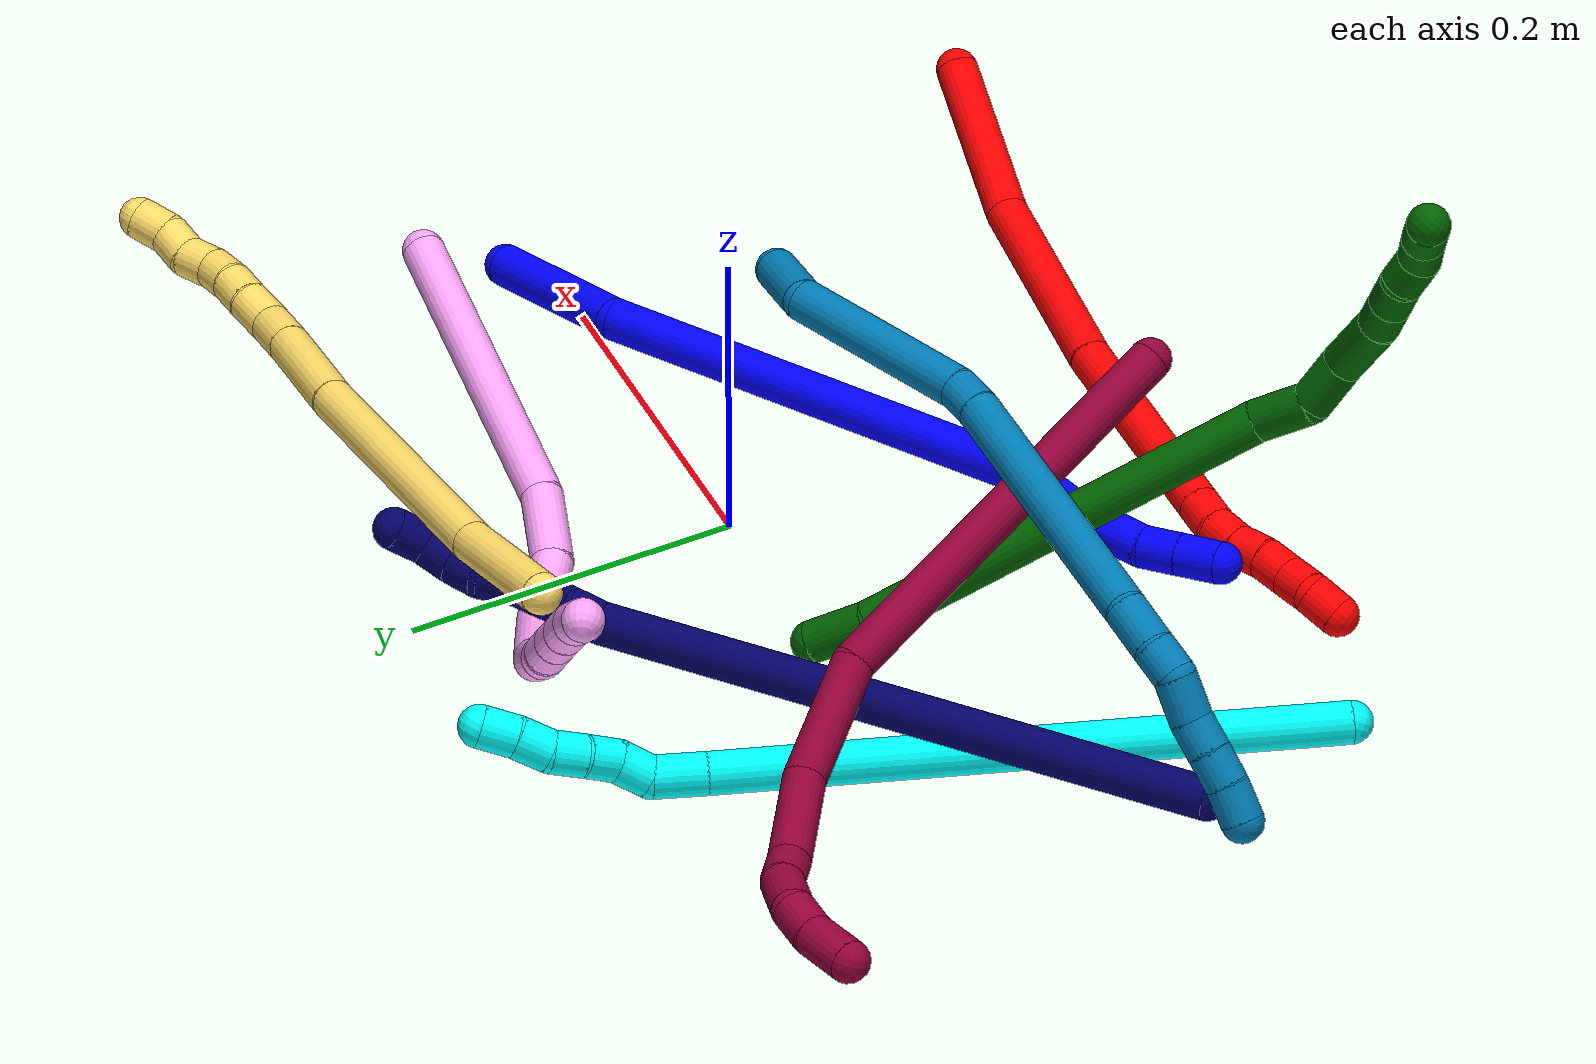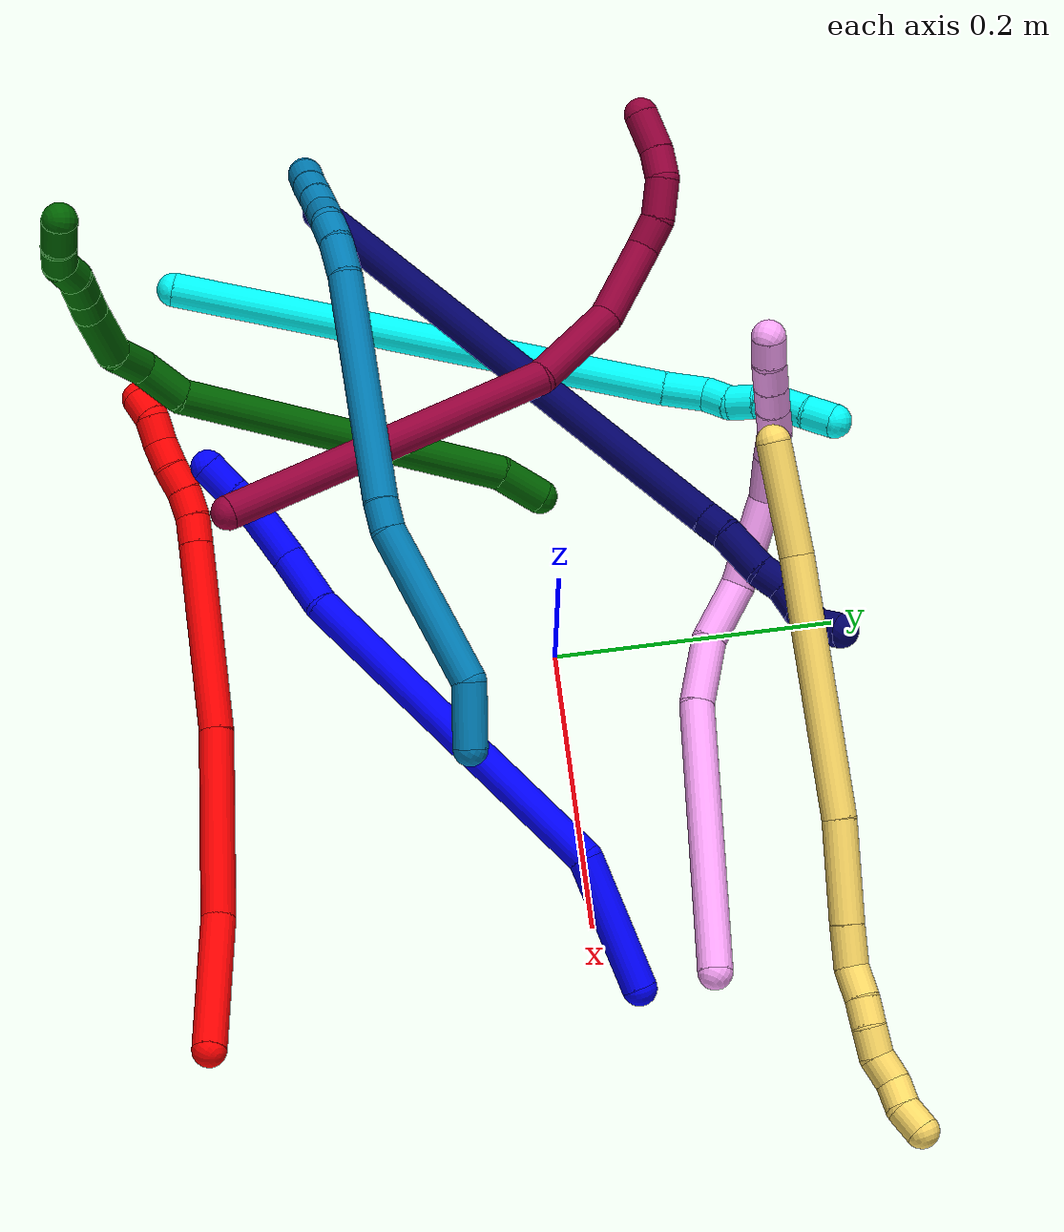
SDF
<sdf version="1.7">
 <world name="default">
  <plugin name="TubeGeneratorPlugin" filename="libtube_generator_plugin.so"/>
  <model name="photoneo_s_sensor">
   <static>1</static>
   <pose>0 0 2 1.57079 1.57079 3.14159</pose>
   <link name="link">
    <inertial><mass>0.1</mass></inertial>
    <sensor name="sensor" type="depth">
     <update_rate>30</update_rate>
     <camera>
      <horizontal_fov>1.22</horizontal_fov>
      <image><width>1920</width><height>1200</height><format>B8G8R8</format></image>
      <clip><near>0.1</near><far>4</far></clip>
      <depth_camera><output>points</output></depth_camera>
     </camera>
     <plugin name="camera_plugin" filename="libgazebo_ros_depth_camera.so">
      <baseline>0.2</baseline>
      <alwaysOn>1</alwaysOn>
      <updateRate>0.0</updateRate>
      <cameraName>camera_ir</cameraName>
      <imageTopicName>/camera/color/image_raw</imageTopicName>
      <cameraInfoTopicName>/camera/color/camera_info</cameraInfoTopicName>
      <depthImageTopicName>/camera/depth/image_raw</depthImageTopicName>
      <depthImageCameraInfoTopicName>/camera/depth/camera_info</depthImageCameraInfoTopicName>
      <pointCloudTopicName>/camera/depth/points</pointCloudTopicName>
      <frameName>fr_optical</frameName>
      <pointCloudCutoff>0.1</pointCloudCutoff>
      <pointCloudCutoffMax>2.0</pointCloudCutoffMax>
      <distortionK1>0</distortionK1>
      <distortionK2>0</distortionK2>
      <distortionK3>0</distortionK3>
      <distortionT1>0</distortionT1>
      <distortionT2>0</distortionT2>
      <CxPrime>0</CxPrime>
      <Cx>0</Cx>
      <Cy>0</Cy>
      <focalLength>0</focalLength>
      <hackBaseline>0</hackBaseline>
     </plugin>
    </sensor>
   </link>
  </model>
  <gravity>0 0 -9.8</gravity>
  <magnetic_field>6e-06 2.3e-05 -4.2e-05</magnetic_field>
  <atmosphere type="adiabatic"/>
  <physics name="default_physics" default="0" type="ode">
   <max_step_size>0.003</max_step_size>
   <real_time_factor>1</real_time_factor>
   <real_time_update_rate>1000</real_time_update_rate>
   <max_contacts>10000</max_contacts>
   <ode>
    <solver>
     <type>quick</type>
     <iters>100</iters>
     <sor>1.3</sor>
     <use_dynamic_moi_rescaling>0</use_dynamic_moi_rescaling>
    </solver>
    <constraints>
     <contact_max_correcting_vel>0</contact_max_correcting_vel>
     <contact_surface_layer>0.001</contact_surface_layer>
     <cfm>0</cfm>
     <erp>0.2</erp>
    </constraints>
   </ode>
  </physics>
  <scene><ambient>0.4 0.4 0.4 1</ambient><background>0.7 0.7 0.7 1</background><shadows>0</shadows></scene>
  <audio><device>default</device></audio>
  <spherical_coordinates>
   <surface_model>EARTH_WGS84</surface_model>
   <latitude_deg>0</latitude_deg>
   <longitude_deg>0</longitude_deg>
   <elevation>0</elevation>
   <heading_deg>0</heading_deg>
  </spherical_coordinates>
  <model name="bin">
   <static>1</static>
   <link name="bottom">
    <collision name="collision-bottom">
     <pose>0 0 -0.01 0 -0 0</pose>
     <geometry><box><size>0.8 0.6 0.02</size></box></geometry>
     <surface>
      <friction><ode><mu>100</mu><mu2>100</mu2></ode></friction>
      <contact><collide_bitmask>65535</collide_bitmask></contact>
     </surface>
    </collision>
   </link>
   <link name="west_wall">
    <collision name="collision-west_wall">
     <pose>-0.41 0 0.1 0 -0 0</pose>
     <geometry><box><size>0.02 0.6 0.2</size></box></geometry>
     <surface>
      <friction><ode><mu>100</mu><mu2>100</mu2></ode></friction>
      <contact><collide_bitmask>65535</collide_bitmask></contact>
     </surface>
    </collision>
   </link>
   <link name="east_wall">
    <collision name="collision-east_wall">
     <pose>0.41 0 0.1 0 -0 0</pose>
     <geometry><box><size>0.02 0.6 0.2</size></box></geometry>
     <surface>
      <friction><ode><mu>100</mu><mu2>100</mu2></ode></friction>
      <contact><collide_bitmask>65535</collide_bitmask></contact>
     </surface>
    </collision>
   </link>
   <link name="south_wall">
    <collision name="collision-south_wall">
     <pose>0 -0.31 0.1 0 -0 0</pose>
     <geometry><box><size>0.8 0.02 0.2</size></box></geometry>
     <surface>
      <friction><ode><mu>100</mu><mu2>100</mu2></ode></friction>
      <contact><collide_bitmask>65535</collide_bitmask></contact>
     </surface>
    </collision>
   </link>
   <link name="north_wall">
    <collision name="collision-north_wall">
     <pose>0 0.31 0.1 0 -0 0</pose>
     <geometry><box><size>0.8 0.02 0.2</size></box></geometry>
     <surface>
      <friction><ode><mu>100</mu><mu2>100</mu2></ode></friction>
      <contact><collide_bitmask>65535</collide_bitmask></contact>
     </surface>
    </collision>
   </link>
  </model>
  <model name="1">
   <static>0</static>
   <link name="1">
    <collision name="collision-cylinder-e_1_1_4">
     <pose>-0.026952 -0.040658 -0.00738 1.75036 -0.577948 -0.684233</pose>
     <geometry><cylinder><radius>0.0125</radius><length>0.09867</length></cylinder></geometry>
     <surface>
      <friction><ode><mu>1.16</mu><mu2>1.16</mu2><slip1>0</slip1><slip2>0</slip2></ode></friction>
      <contact><ode><kp>1e+06</kp><kd>1</kd><max_vel>0</max_vel><min_depth>0.001</min_depth></ode></contact>
     </surface>
    </collision>
    <visual name="visual-cylinder-e_1_1_4">
     <pose>-0.026952 -0.040658 -0.00738 1.75036 -0.577948 -0.684233</pose>
     <geometry><cylinder><radius>0.0125</radius><length>0.09867</length></cylinder></geometry>
     <material><ambient>0 0 1 1</ambient></material>
    </visual>
    <collision name="collision-cylinder-e_2_4_5">
     <pose>-0.138691 -0.156689 -0.084368 2.31645 -0.690632 -1.37588</pose>
     <geometry><cylinder><radius>0.0125</radius><length>0.266196</length></cylinder></geometry>
     <surface>
      <friction><ode><mu>1.16</mu><mu2>1.16</mu2><slip1>0</slip1><slip2>0</slip2></ode></friction>
      <contact><ode><kp>1e+06</kp><kd>1</kd><max_vel>0</max_vel><min_depth>0.001</min_depth></ode></contact>
     </surface>
    </collision>
    <visual name="visual-cylinder-e_2_4_5">
     <pose>-0.138691 -0.156689 -0.084368 2.31645 -0.690632 -1.37588</pose>
     <geometry><cylinder><radius>0.0125</radius><length>0.266196</length></cylinder></geometry>
     <material><ambient>0 0 1 1</ambient></material>
    </visual>
    <collision name="collision-cylinder-e_3_5_6">
     <pose>-0.241615 -0.242906 -0.161461 2.17501 -0.942513 -1.5413</pose>
     <geometry><cylinder><radius>0.0125</radius><length>0.044837</length></cylinder></geometry>
     <surface>
      <friction><ode><mu>1.16</mu><mu2>1.16</mu2><slip1>0</slip1><slip2>0</slip2></ode></friction>
      <contact><ode><kp>1e+06</kp><kd>1</kd><max_vel>0</max_vel><min_depth>0.001</min_depth></ode></contact>
     </surface>
    </collision>
    <visual name="visual-cylinder-e_3_5_6">
     <pose>-0.241615 -0.242906 -0.161461 2.17501 -0.942513 -1.5413</pose>
     <geometry><cylinder><radius>0.0125</radius><length>0.044837</length></cylinder></geometry>
     <material><ambient>0 0 1 1</ambient></material>
    </visual>
    <collision name="collision-cylinder-e_4_6_7">
     <pose>-0.273389 -0.267106 -0.176761 2.10011 -0.72237 -1.16484</pose>
     <geometry><cylinder><radius>0.0125</radius><length>0.041251</length></cylinder></geometry>
     <surface>
      <friction><ode><mu>1.16</mu><mu2>1.16</mu2><slip1>0</slip1><slip2>0</slip2></ode></friction>
      <contact><ode><kp>1e+06</kp><kd>1</kd><max_vel>0</max_vel><min_depth>0.001</min_depth></ode></contact>
     </surface>
    </collision>
    <visual name="visual-cylinder-e_4_6_7">
     <pose>-0.273389 -0.267106 -0.176761 2.10011 -0.72237 -1.16484</pose>
     <geometry><cylinder><radius>0.0125</radius><length>0.041251</length></cylinder></geometry>
     <material><ambient>0 0 1 1</ambient></material>
    </visual>
    <collision name="collision-cylinder-e_5_7_8">
     <pose>-0.292974 -0.28825 -0.191028 2.26281 -0.5316 -1.04996</pose>
     <geometry><cylinder><radius>0.0125</radius><length>0.023466</length></cylinder></geometry>
     <surface>
      <friction><ode><mu>1.16</mu><mu2>1.16</mu2><slip1>0</slip1><slip2>0</slip2></ode></friction>
      <contact><ode><kp>1e+06</kp><kd>1</kd><max_vel>0</max_vel><min_depth>0.001</min_depth></ode></contact>
     </surface>
    </collision>
    <visual name="visual-cylinder-e_5_7_8">
     <pose>-0.292974 -0.28825 -0.191028 2.26281 -0.5316 -1.04996</pose>
     <geometry><cylinder><radius>0.0125</radius><length>0.023466</length></cylinder></geometry>
     <material><ambient>0 0 1 1</ambient></material>
    </visual>
    <collision name="collision-cylinder-e_6_8_2">
     <pose>-0.305209 -0.305094 -0.203963 2.19202 -0.513949 -0.945214</pose>
     <geometry><cylinder><radius>0.0125</radius><length>0.02558</length></cylinder></geometry>
     <surface>
      <friction><ode><mu>1.16</mu><mu2>1.16</mu2><slip1>0</slip1><slip2>0</slip2></ode></friction>
      <contact><ode><kp>1e+06</kp><kd>1</kd><max_vel>0</max_vel><min_depth>0.001</min_depth></ode></contact>
     </surface>
    </collision>
    <visual name="visual-cylinder-e_6_8_2">
     <pose>-0.305209 -0.305094 -0.203963 2.19202 -0.513949 -0.945214</pose>
     <geometry><cylinder><radius>0.0125</radius><length>0.02558</length></cylinder></geometry>
     <material><ambient>0 0 1 1</ambient></material>
    </visual>
    <collision name="collision-sphere-2">
     <pose>-0.311497 -0.31415 -0.210446 0 -0 0</pose>
     <geometry><sphere><radius>0.0125</radius></sphere></geometry>
     <surface>
      <friction><ode><mu>1.16</mu><mu2>1.16</mu2><slip1>0</slip1><slip2>0</slip2></ode></friction>
      <contact><ode><kp>1e+06</kp><kd>1</kd><max_vel>0</max_vel><min_depth>0.001</min_depth></ode></contact>
     </surface>
    </collision>
    <visual name="visual-sphere-2">
     <pose>-0.311497 -0.31415 -0.210446 0 -0 0</pose>
     <geometry><sphere><radius>0.0125</radius></sphere></geometry>
     <material><ambient>0 0 1 1</ambient></material>
    </visual>
    <collision name="collision-sphere-4">
     <pose>-0.053904 -0.081316 -0.014761 0 -0 0</pose>
     <geometry><sphere><radius>0.0125</radius></sphere></geometry>
     <surface>
      <friction><ode><mu>1.16</mu><mu2>1.16</mu2><slip1>0</slip1><slip2>0</slip2></ode></friction>
      <contact><ode><kp>1e+06</kp><kd>1</kd><max_vel>0</max_vel><min_depth>0.001</min_depth></ode></contact>
     </surface>
    </collision>
    <visual name="visual-sphere-4">
     <pose>-0.053904 -0.081316 -0.014761 0 -0 0</pose>
     <geometry><sphere><radius>0.0125</radius></sphere></geometry>
     <material><ambient>0 0 1 1</ambient></material>
    </visual>
    <collision name="collision-sphere-1">
     <geometry><sphere><radius>0.0125</radius></sphere></geometry>
     <surface>
      <friction><ode><mu>1.16</mu><mu2>1.16</mu2><slip1>0</slip1><slip2>0</slip2></ode></friction>
      <contact><ode><kp>1e+06</kp><kd>1</kd><max_vel>0</max_vel><min_depth>0.001</min_depth></ode></contact>
     </surface>
    </collision>
    <visual name="visual-sphere-1">
     <geometry><sphere><radius>0.0125</radius></sphere></geometry>
     <material><ambient>0 0 1 1</ambient></material>
    </visual>
    <collision name="collision-sphere-8">
     <pose>-0.298921 -0.296037 -0.197481 0 -0 0</pose>
     <geometry><sphere><radius>0.0125</radius></sphere></geometry>
     <surface>
      <friction><ode><mu>1.16</mu><mu2>1.16</mu2><slip1>0</slip1><slip2>0</slip2></ode></friction>
      <contact><ode><kp>1e+06</kp><kd>1</kd><max_vel>0</max_vel><min_depth>0.001</min_depth></ode></contact>
     </surface>
    </collision>
    <visual name="visual-sphere-8">
     <pose>-0.298921 -0.296037 -0.197481 0 -0 0</pose>
     <geometry><sphere><radius>0.0125</radius></sphere></geometry>
     <material><ambient>0 0 1 1</ambient></material>
    </visual>
    <collision name="collision-sphere-5">
     <pose>-0.223477 -0.232062 -0.153975 0 -0 0</pose>
     <geometry><sphere><radius>0.0125</radius></sphere></geometry>
     <surface>
      <friction><ode><mu>1.16</mu><mu2>1.16</mu2><slip1>0</slip1><slip2>0</slip2></ode></friction>
      <contact><ode><kp>1e+06</kp><kd>1</kd><max_vel>0</max_vel><min_depth>0.001</min_depth></ode></contact>
     </surface>
    </collision>
    <visual name="visual-sphere-5">
     <pose>-0.223477 -0.232062 -0.153975 0 -0 0</pose>
     <geometry><sphere><radius>0.0125</radius></sphere></geometry>
     <material><ambient>0 0 1 1</ambient></material>
    </visual>
    <collision name="collision-sphere-6">
     <pose>-0.259752 -0.253749 -0.168947 0 -0 0</pose>
     <geometry><sphere><radius>0.0125</radius></sphere></geometry>
     <surface>
      <friction><ode><mu>1.16</mu><mu2>1.16</mu2><slip1>0</slip1><slip2>0</slip2></ode></friction>
      <contact><ode><kp>1e+06</kp><kd>1</kd><max_vel>0</max_vel><min_depth>0.001</min_depth></ode></contact>
     </surface>
    </collision>
    <visual name="visual-sphere-6">
     <pose>-0.259752 -0.253749 -0.168947 0 -0 0</pose>
     <geometry><sphere><radius>0.0125</radius></sphere></geometry>
     <material><ambient>0 0 1 1</ambient></material>
    </visual>
    <collision name="collision-sphere-7">
     <pose>-0.287026 -0.280463 -0.184574 0 -0 0</pose>
     <geometry><sphere><radius>0.0125</radius></sphere></geometry>
     <surface>
      <friction><ode><mu>1.16</mu><mu2>1.16</mu2><slip1>0</slip1><slip2>0</slip2></ode></friction>
      <contact><ode><kp>1e+06</kp><kd>1</kd><max_vel>0</max_vel><min_depth>0.001</min_depth></ode></contact>
     </surface>
    </collision>
    <visual name="visual-sphere-7">
     <pose>-0.287026 -0.280463 -0.184574 0 -0 0</pose>
     <geometry><sphere><radius>0.0125</radius></sphere></geometry>
     <material><ambient>0 0 1 1</ambient></material>
    </visual>
    <inertial>
     <pose>-0.152743 -0.164399 -0.094835 0 -0 0</pose>
     <mass>0.5</mass>
     <inertia>
      <ixx>-0.000984</ixx>
      <ixy>0</ixy>
      <ixz>0</ixz>
      <iyy>-0.000735</iyy>
      <iyz>0</iyz>
      <izz>0.002029</izz>
     </inertia>
    </inertial>
   </link>
   <pose>0.249371 0.026845 0.011892 -1.48263 -0.740297 0.047758</pose>
  </model>
  <model name="2">
   <static>0</static>
   <link name="2">
    <collision name="collision-cylinder-e_1_1_4">
     <pose>-0.016019 -0.033835 0.036101 0.753013 -0.313116 -0.124656</pose>
     <geometry><cylinder><radius>0.0125</radius><length>0.104014</length></cylinder></geometry>
     <surface>
      <friction><ode><mu>1.16</mu><mu2>1.16</mu2><slip1>0</slip1><slip2>0</slip2></ode></friction>
      <contact><ode><kp>1e+06</kp><kd>1</kd><max_vel>0</max_vel><min_depth>0.001</min_depth></ode></contact>
     </surface>
    </collision>
    <visual name="visual-cylinder-e_1_1_4">
     <pose>-0.016019 -0.033835 0.036101 0.753013 -0.313116 -0.124656</pose>
     <geometry><cylinder><radius>0.0125</radius><length>0.104014</length></cylinder></geometry>
     <material><ambient>1 0 0 1</ambient></material>
    </visual>
    <collision name="collision-cylinder-e_2_4_5">
     <pose>-0.071124 -0.105303 0.113143 0.743317 -0.61264 -0.245313</pose>
     <geometry><cylinder><radius>0.0125</radius><length>0.135943</length></cylinder></geometry>
     <surface>
      <friction><ode><mu>1.16</mu><mu2>1.16</mu2><slip1>0</slip1><slip2>0</slip2></ode></friction>
      <contact><ode><kp>1e+06</kp><kd>1</kd><max_vel>0</max_vel><min_depth>0.001</min_depth></ode></contact>
     </surface>
    </collision>
    <visual name="visual-cylinder-e_2_4_5">
     <pose>-0.071124 -0.105303 0.113143 0.743317 -0.61264 -0.245313</pose>
     <geometry><cylinder><radius>0.0125</radius><length>0.135943</length></cylinder></geometry>
     <material><ambient>1 0 0 1</ambient></material>
    </visual>
    <collision name="collision-cylinder-e_3_5_6">
     <pose>-0.150561 -0.176005 0.199774 0.6265 -0.621011 -0.207135</pose>
     <geometry><cylinder><radius>0.0125</radius><length>0.138697</length></cylinder></geometry>
     <surface>
      <friction><ode><mu>1.16</mu><mu2>1.16</mu2><slip1>0</slip1><slip2>0</slip2></ode></friction>
      <contact><ode><kp>1e+06</kp><kd>1</kd><max_vel>0</max_vel><min_depth>0.001</min_depth></ode></contact>
     </surface>
    </collision>
    <visual name="visual-cylinder-e_3_5_6">
     <pose>-0.150561 -0.176005 0.199774 0.6265 -0.621011 -0.207135</pose>
     <geometry><cylinder><radius>0.0125</radius><length>0.138697</length></cylinder></geometry>
     <material><ambient>1 0 0 1</ambient></material>
    </visual>
    <collision name="collision-cylinder-e_4_6_7">
     <pose>-0.197029 -0.213977 0.252345 0.619085 -0.626537 -0.206467</pose>
     <geometry><cylinder><radius>0.0125</radius><length>0.020864</length></cylinder></geometry>
     <surface>
      <friction><ode><mu>1.16</mu><mu2>1.16</mu2><slip1>0</slip1><slip2>0</slip2></ode></friction>
      <contact><ode><kp>1e+06</kp><kd>1</kd><max_vel>0</max_vel><min_depth>0.001</min_depth></ode></contact>
     </surface>
    </collision>
    <visual name="visual-cylinder-e_4_6_7">
     <pose>-0.197029 -0.213977 0.252345 0.619085 -0.626537 -0.206467</pose>
     <geometry><cylinder><radius>0.0125</radius><length>0.020864</length></cylinder></geometry>
     <material><ambient>1 0 0 1</ambient></material>
    </visual>
    <collision name="collision-cylinder-e_5_7_8">
     <pose>-0.209403 -0.221798 0.266757 0.369665 -0.659275 -0.127756</pose>
     <geometry><cylinder><radius>0.0125</radius><length>0.020433</length></cylinder></geometry>
     <surface>
      <friction><ode><mu>1.16</mu><mu2>1.16</mu2><slip1>0</slip1><slip2>0</slip2></ode></friction>
      <contact><ode><kp>1e+06</kp><kd>1</kd><max_vel>0</max_vel><min_depth>0.001</min_depth></ode></contact>
     </surface>
    </collision>
    <visual name="visual-cylinder-e_5_7_8">
     <pose>-0.209403 -0.221798 0.266757 0.369665 -0.659275 -0.127756</pose>
     <geometry><cylinder><radius>0.0125</radius><length>0.020433</length></cylinder></geometry>
     <material><ambient>1 0 0 1</ambient></material>
    </visual>
    <collision name="collision-cylinder-e_6_8_9">
     <pose>-0.222119 -0.225587 0.281877 0.114259 -0.701717 -0.041859</pose>
     <geometry><cylinder><radius>0.0125</radius><length>0.020005</length></cylinder></geometry>
     <surface>
      <friction><ode><mu>1.16</mu><mu2>1.16</mu2><slip1>0</slip1><slip2>0</slip2></ode></friction>
      <contact><ode><kp>1e+06</kp><kd>1</kd><max_vel>0</max_vel><min_depth>0.001</min_depth></ode></contact>
     </surface>
    </collision>
    <visual name="visual-cylinder-e_6_8_9">
     <pose>-0.222119 -0.225587 0.281877 0.114259 -0.701717 -0.041859</pose>
     <geometry><cylinder><radius>0.0125</radius><length>0.020005</length></cylinder></geometry>
     <material><ambient>1 0 0 1</ambient></material>
    </visual>
    <collision name="collision-cylinder-e_7_9_10">
     <pose>-0.234332 -0.228708 0.297354 0.277827 -0.611965 -0.088278</pose>
     <geometry><cylinder><radius>0.0125</radius><length>0.020043</length></cylinder></geometry>
     <surface>
      <friction><ode><mu>1.16</mu><mu2>1.16</mu2><slip1>0</slip1><slip2>0</slip2></ode></friction>
      <contact><ode><kp>1e+06</kp><kd>1</kd><max_vel>0</max_vel><min_depth>0.001</min_depth></ode></contact>
     </surface>
    </collision>
    <visual name="visual-cylinder-e_7_9_10">
     <pose>-0.234332 -0.228708 0.297354 0.277827 -0.611965 -0.088278</pose>
     <geometry><cylinder><radius>0.0125</radius><length>0.020043</length></cylinder></geometry>
     <material><ambient>1 0 0 1</ambient></material>
    </visual>
    <collision name="collision-cylinder-e_8_10_11">
     <pose>-0.246935 -0.233658 0.312014 0.379563 -0.753996 -0.151821</pose>
     <geometry><cylinder><radius>0.0125</radius><length>0.020001</length></cylinder></geometry>
     <surface>
      <friction><ode><mu>1.16</mu><mu2>1.16</mu2><slip1>0</slip1><slip2>0</slip2></ode></friction>
      <contact><ode><kp>1e+06</kp><kd>1</kd><max_vel>0</max_vel><min_depth>0.001</min_depth></ode></contact>
     </surface>
    </collision>
    <visual name="visual-cylinder-e_8_10_11">
     <pose>-0.246935 -0.233658 0.312014 0.379563 -0.753996 -0.151821</pose>
     <geometry><cylinder><radius>0.0125</radius><length>0.020001</length></cylinder></geometry>
     <material><ambient>1 0 0 1</ambient></material>
    </visual>
    <collision name="collision-cylinder-e_9_11_2">
     <pose>-0.256883 -0.237924 0.328162 0.165316 -0.315379 -0.026345</pose>
     <geometry><cylinder><radius>0.0125</radius><length>0.02</length></cylinder></geometry>
     <surface>
      <friction><ode><mu>1.16</mu><mu2>1.16</mu2><slip1>0</slip1><slip2>0</slip2></ode></friction>
      <contact><ode><kp>1e+06</kp><kd>1</kd><max_vel>0</max_vel><min_depth>0.001</min_depth></ode></contact>
     </surface>
    </collision>
    <visual name="visual-cylinder-e_9_11_2">
     <pose>-0.256883 -0.237924 0.328162 0.165316 -0.315379 -0.026345</pose>
     <geometry><cylinder><radius>0.0125</radius><length>0.02</length></cylinder></geometry>
     <material><ambient>1 0 0 1</ambient></material>
    </visual>
    <collision name="collision-sphere-2">
     <pose>-0.259985 -0.239488 0.33754 0 -0 0</pose>
     <geometry><sphere><radius>0.0125</radius></sphere></geometry>
     <surface>
      <friction><ode><mu>1.16</mu><mu2>1.16</mu2><slip1>0</slip1><slip2>0</slip2></ode></friction>
      <contact><ode><kp>1e+06</kp><kd>1</kd><max_vel>0</max_vel><min_depth>0.001</min_depth></ode></contact>
     </surface>
    </collision>
    <visual name="visual-sphere-2">
     <pose>-0.259985 -0.239488 0.33754 0 -0 0</pose>
     <geometry><sphere><radius>0.0125</radius></sphere></geometry>
     <material><ambient>1 0 0 1</ambient></material>
    </visual>
    <collision name="collision-sphere-11">
     <pose>-0.253781 -0.23636 0.318785 0 -0 0</pose>
     <geometry><sphere><radius>0.0125</radius></sphere></geometry>
     <surface>
      <friction><ode><mu>1.16</mu><mu2>1.16</mu2><slip1>0</slip1><slip2>0</slip2></ode></friction>
      <contact><ode><kp>1e+06</kp><kd>1</kd><max_vel>0</max_vel><min_depth>0.001</min_depth></ode></contact>
     </surface>
    </collision>
    <visual name="visual-sphere-11">
     <pose>-0.253781 -0.23636 0.318785 0 -0 0</pose>
     <geometry><sphere><radius>0.0125</radius></sphere></geometry>
     <material><ambient>1 0 0 1</ambient></material>
    </visual>
    <collision name="collision-sphere-10">
     <pose>-0.240089 -0.230957 0.305243 0 -0 0</pose>
     <geometry><sphere><radius>0.0125</radius></sphere></geometry>
     <surface>
      <friction><ode><mu>1.16</mu><mu2>1.16</mu2><slip1>0</slip1><slip2>0</slip2></ode></friction>
      <contact><ode><kp>1e+06</kp><kd>1</kd><max_vel>0</max_vel><min_depth>0.001</min_depth></ode></contact>
     </surface>
    </collision>
    <visual name="visual-sphere-10">
     <pose>-0.240089 -0.230957 0.305243 0 -0 0</pose>
     <geometry><sphere><radius>0.0125</radius></sphere></geometry>
     <material><ambient>1 0 0 1</ambient></material>
    </visual>
    <collision name="collision-sphere-9">
     <pose>-0.228575 -0.226458 0.289466 0 -0 0</pose>
     <geometry><sphere><radius>0.0125</radius></sphere></geometry>
     <surface>
      <friction><ode><mu>1.16</mu><mu2>1.16</mu2><slip1>0</slip1><slip2>0</slip2></ode></friction>
      <contact><ode><kp>1e+06</kp><kd>1</kd><max_vel>0</max_vel><min_depth>0.001</min_depth></ode></contact>
     </surface>
    </collision>
    <visual name="visual-sphere-9">
     <pose>-0.228575 -0.226458 0.289466 0 -0 0</pose>
     <geometry><sphere><radius>0.0125</radius></sphere></geometry>
     <material><ambient>1 0 0 1</ambient></material>
    </visual>
    <collision name="collision-sphere-4">
     <pose>-0.032039 -0.06767 0.072202 0 -0 0</pose>
     <geometry><sphere><radius>0.0125</radius></sphere></geometry>
     <surface>
      <friction><ode><mu>1.16</mu><mu2>1.16</mu2><slip1>0</slip1><slip2>0</slip2></ode></friction>
      <contact><ode><kp>1e+06</kp><kd>1</kd><max_vel>0</max_vel><min_depth>0.001</min_depth></ode></contact>
     </surface>
    </collision>
    <visual name="visual-sphere-4">
     <pose>-0.032039 -0.06767 0.072202 0 -0 0</pose>
     <geometry><sphere><radius>0.0125</radius></sphere></geometry>
     <material><ambient>1 0 0 1</ambient></material>
    </visual>
    <collision name="collision-sphere-1">
     <geometry><sphere><radius>0.0125</radius></sphere></geometry>
     <surface>
      <friction><ode><mu>1.16</mu><mu2>1.16</mu2><slip1>0</slip1><slip2>0</slip2></ode></friction>
      <contact><ode><kp>1e+06</kp><kd>1</kd><max_vel>0</max_vel><min_depth>0.001</min_depth></ode></contact>
     </surface>
    </collision>
    <visual name="visual-sphere-1">
     <geometry><sphere><radius>0.0125</radius></sphere></geometry>
     <material><ambient>1 0 0 1</ambient></material>
    </visual>
    <collision name="collision-sphere-8">
     <pose>-0.215662 -0.224716 0.274288 0 -0 0</pose>
     <geometry><sphere><radius>0.0125</radius></sphere></geometry>
     <surface>
      <friction><ode><mu>1.16</mu><mu2>1.16</mu2><slip1>0</slip1><slip2>0</slip2></ode></friction>
      <contact><ode><kp>1e+06</kp><kd>1</kd><max_vel>0</max_vel><min_depth>0.001</min_depth></ode></contact>
     </surface>
    </collision>
    <visual name="visual-sphere-8">
     <pose>-0.215662 -0.224716 0.274288 0 -0 0</pose>
     <geometry><sphere><radius>0.0125</radius></sphere></geometry>
     <material><ambient>1 0 0 1</ambient></material>
    </visual>
    <collision name="collision-sphere-5">
     <pose>-0.11021 -0.142936 0.154085 0 -0 0</pose>
     <geometry><sphere><radius>0.0125</radius></sphere></geometry>
     <surface>
      <friction><ode><mu>1.16</mu><mu2>1.16</mu2><slip1>0</slip1><slip2>0</slip2></ode></friction>
      <contact><ode><kp>1e+06</kp><kd>1</kd><max_vel>0</max_vel><min_depth>0.001</min_depth></ode></contact>
     </surface>
    </collision>
    <visual name="visual-sphere-5">
     <pose>-0.11021 -0.142936 0.154085 0 -0 0</pose>
     <geometry><sphere><radius>0.0125</radius></sphere></geometry>
     <material><ambient>1 0 0 1</ambient></material>
    </visual>
    <collision name="collision-sphere-6">
     <pose>-0.190912 -0.209073 0.245463 0 -0 0</pose>
     <geometry><sphere><radius>0.0125</radius></sphere></geometry>
     <surface>
      <friction><ode><mu>1.16</mu><mu2>1.16</mu2><slip1>0</slip1><slip2>0</slip2></ode></friction>
      <contact><ode><kp>1e+06</kp><kd>1</kd><max_vel>0</max_vel><min_depth>0.001</min_depth></ode></contact>
     </surface>
    </collision>
    <visual name="visual-sphere-6">
     <pose>-0.190912 -0.209073 0.245463 0 -0 0</pose>
     <geometry><sphere><radius>0.0125</radius></sphere></geometry>
     <material><ambient>1 0 0 1</ambient></material>
    </visual>
    <collision name="collision-sphere-7">
     <pose>-0.203145 -0.21888 0.259227 0 -0 0</pose>
     <geometry><sphere><radius>0.0125</radius></sphere></geometry>
     <surface>
      <friction><ode><mu>1.16</mu><mu2>1.16</mu2><slip1>0</slip1><slip2>0</slip2></ode></friction>
      <contact><ode><kp>1e+06</kp><kd>1</kd><max_vel>0</max_vel><min_depth>0.001</min_depth></ode></contact>
     </surface>
    </collision>
    <visual name="visual-sphere-7">
     <pose>-0.203145 -0.21888 0.259227 0 -0 0</pose>
     <geometry><sphere><radius>0.0125</radius></sphere></geometry>
     <material><ambient>1 0 0 1</ambient></material>
    </visual>
    <inertial>
     <pose>-0.119648 -0.139542 0.163925 0 -0 0</pose>
     <mass>0.5</mass>
     <inertia>
      <ixx>0.000338</ixx>
      <ixy>0</ixy>
      <ixz>0</ixz>
      <iyy>0.00034</iyy>
      <iyz>0</iyz>
      <izz>0.000611</izz>
     </inertia>
    </inertial>
   </link>
   <pose>0.260403 -0.275768 0.042769 2.65567 0.941581 0.108548</pose>
  </model>
  <model name="3">
   <static>0</static>
   <link name="3">
    <collision name="collision-cylinder-e_1_1_4">
     <pose>0.031161 0.158458 0.084653 -1.08014 0.171743 -0.103126</pose>
     <geometry><cylinder><radius>0.0125</radius><length>0.36467</length></cylinder></geometry>
     <surface>
      <friction><ode><mu>1.16</mu><mu2>1.16</mu2><slip1>0</slip1><slip2>0</slip2></ode></friction>
      <contact><ode><kp>1e+06</kp><kd>1</kd><max_vel>0</max_vel><min_depth>0.001</min_depth></ode></contact>
     </surface>
    </collision>
    <visual name="visual-cylinder-e_1_1_4">
     <pose>0.031161 0.158458 0.084653 -1.08014 0.171743 -0.103126</pose>
     <geometry><cylinder><radius>0.0125</radius><length>0.36467</length></cylinder></geometry>
     <material><ambient>0.003922 1 0.996078 1</ambient></material>
    </visual>
    <collision name="collision-cylinder-e_2_4_5">
     <pose>0.066084 0.330726 0.176191 -1.1083 0.239134 -0.148419</pose>
     <geometry><cylinder><radius>0.0125</radius><length>0.031768</length></cylinder></geometry>
     <surface>
      <friction><ode><mu>1.16</mu><mu2>1.16</mu2><slip1>0</slip1><slip2>0</slip2></ode></friction>
      <contact><ode><kp>1e+06</kp><kd>1</kd><max_vel>0</max_vel><min_depth>0.001</min_depth></ode></contact>
     </surface>
    </collision>
    <visual name="visual-cylinder-e_2_4_5">
     <pose>0.066084 0.330726 0.176191 -1.1083 0.239134 -0.148419</pose>
     <geometry><cylinder><radius>0.0125</radius><length>0.031768</length></cylinder></geometry>
     <material><ambient>0.003922 1 0.996078 1</ambient></material>
    </visual>
    <collision name="collision-cylinder-e_3_5_6">
     <pose>0.071377 0.354895 0.1825 -1.62641 0.146449 -0.154796</pose>
     <geometry><cylinder><radius>0.0125</radius><length>0.020973</length></cylinder></geometry>
     <surface>
      <friction><ode><mu>1.16</mu><mu2>1.16</mu2><slip1>0</slip1><slip2>0</slip2></ode></friction>
      <contact><ode><kp>1e+06</kp><kd>1</kd><max_vel>0</max_vel><min_depth>0.001</min_depth></ode></contact>
     </surface>
    </collision>
    <visual name="visual-cylinder-e_3_5_6">
     <pose>0.071377 0.354895 0.1825 -1.62641 0.146449 -0.154796</pose>
     <geometry><cylinder><radius>0.0125</radius><length>0.020973</length></cylinder></geometry>
     <material><ambient>0.003922 1 0.996078 1</ambient></material>
    </visual>
    <collision name="collision-cylinder-e_4_6_7">
     <pose>0.077542 0.373993 0.183513 -1.39089 0.480851 -0.403631</pose>
     <geometry><cylinder><radius>0.0125</radius><length>0.02004</length></cylinder></geometry>
     <surface>
      <friction><ode><mu>1.16</mu><mu2>1.16</mu2><slip1>0</slip1><slip2>0</slip2></ode></friction>
      <contact><ode><kp>1e+06</kp><kd>1</kd><max_vel>0</max_vel><min_depth>0.001</min_depth></ode></contact>
     </surface>
    </collision>
    <visual name="visual-cylinder-e_4_6_7">
     <pose>0.077542 0.373993 0.183513 -1.39089 0.480851 -0.403631</pose>
     <geometry><cylinder><radius>0.0125</radius><length>0.02004</length></cylinder></geometry>
     <material><ambient>0.003922 1 0.996078 1</ambient></material>
    </visual>
    <collision name="collision-cylinder-e_5_7_8">
     <pose>0.085291 0.392071 0.187442 -1.32531 0.312947 -0.244992</pose>
     <geometry><cylinder><radius>0.0125</radius><length>0.020234</length></cylinder></geometry>
     <surface>
      <friction><ode><mu>1.16</mu><mu2>1.16</mu2><slip1>0</slip1><slip2>0</slip2></ode></friction>
      <contact><ode><kp>1e+06</kp><kd>1</kd><max_vel>0</max_vel><min_depth>0.001</min_depth></ode></contact>
     </surface>
    </collision>
    <visual name="visual-cylinder-e_5_7_8">
     <pose>0.085291 0.392071 0.187442 -1.32531 0.312947 -0.244992</pose>
     <geometry><cylinder><radius>0.0125</radius><length>0.020234</length></cylinder></geometry>
     <material><ambient>0.003922 1 0.996078 1</ambient></material>
    </visual>
    <collision name="collision-cylinder-e_6_8_9">
     <pose>0.090148 0.411595 0.189638 -1.58493 0.169389 -0.171788</pose>
     <geometry><cylinder><radius>0.0125</radius><length>0.020671</length></cylinder></geometry>
     <surface>
      <friction><ode><mu>1.16</mu><mu2>1.16</mu2><slip1>0</slip1><slip2>0</slip2></ode></friction>
      <contact><ode><kp>1e+06</kp><kd>1</kd><max_vel>0</max_vel><min_depth>0.001</min_depth></ode></contact>
     </surface>
    </collision>
    <visual name="visual-cylinder-e_6_8_9">
     <pose>0.090148 0.411595 0.189638 -1.58493 0.169389 -0.171788</pose>
     <geometry><cylinder><radius>0.0125</radius><length>0.020671</length></cylinder></geometry>
     <material><ambient>0.003922 1 0.996078 1</ambient></material>
    </visual>
    <collision name="collision-cylinder-e_7_9_2">
     <pose>0.093497 0.432401 0.190823 -1.44631 0.149036 -0.131603</pose>
     <geometry><cylinder><radius>0.0125</radius><length>0.021644</length></cylinder></geometry>
     <surface>
      <friction><ode><mu>1.16</mu><mu2>1.16</mu2><slip1>0</slip1><slip2>0</slip2></ode></friction>
      <contact><ode><kp>1e+06</kp><kd>1</kd><max_vel>0</max_vel><min_depth>0.001</min_depth></ode></contact>
     </surface>
    </collision>
    <visual name="visual-cylinder-e_7_9_2">
     <pose>0.093497 0.432401 0.190823 -1.44631 0.149036 -0.131603</pose>
     <geometry><cylinder><radius>0.0125</radius><length>0.021644</length></cylinder></geometry>
     <material><ambient>0.003922 1 0.996078 1</ambient></material>
    </visual>
    <collision name="collision-sphere-2">
     <pose>0.095104 0.44302 0.192151 0 -0 0</pose>
     <geometry><sphere><radius>0.0125</radius></sphere></geometry>
     <surface>
      <friction><ode><mu>1.16</mu><mu2>1.16</mu2><slip1>0</slip1><slip2>0</slip2></ode></friction>
      <contact><ode><kp>1e+06</kp><kd>1</kd><max_vel>0</max_vel><min_depth>0.001</min_depth></ode></contact>
     </surface>
    </collision>
    <visual name="visual-sphere-2">
     <pose>0.095104 0.44302 0.192151 0 -0 0</pose>
     <geometry><sphere><radius>0.0125</radius></sphere></geometry>
     <material><ambient>0.003922 1 0.996078 1</ambient></material>
    </visual>
    <collision name="collision-sphere-9">
     <pose>0.09189 0.421781 0.189494 0 -0 0</pose>
     <geometry><sphere><radius>0.0125</radius></sphere></geometry>
     <surface>
      <friction><ode><mu>1.16</mu><mu2>1.16</mu2><slip1>0</slip1><slip2>0</slip2></ode></friction>
      <contact><ode><kp>1e+06</kp><kd>1</kd><max_vel>0</max_vel><min_depth>0.001</min_depth></ode></contact>
     </surface>
    </collision>
    <visual name="visual-sphere-9">
     <pose>0.09189 0.421781 0.189494 0 -0 0</pose>
     <geometry><sphere><radius>0.0125</radius></sphere></geometry>
     <material><ambient>0.003922 1 0.996078 1</ambient></material>
    </visual>
    <collision name="collision-sphere-4">
     <pose>0.062322 0.316915 0.169306 0 -0 0</pose>
     <geometry><sphere><radius>0.0125</radius></sphere></geometry>
     <surface>
      <friction><ode><mu>1.16</mu><mu2>1.16</mu2><slip1>0</slip1><slip2>0</slip2></ode></friction>
      <contact><ode><kp>1e+06</kp><kd>1</kd><max_vel>0</max_vel><min_depth>0.001</min_depth></ode></contact>
     </surface>
    </collision>
    <visual name="visual-sphere-4">
     <pose>0.062322 0.316915 0.169306 0 -0 0</pose>
     <geometry><sphere><radius>0.0125</radius></sphere></geometry>
     <material><ambient>0.003922 1 0.996078 1</ambient></material>
    </visual>
    <collision name="collision-sphere-1">
     <geometry><sphere><radius>0.0125</radius></sphere></geometry>
     <surface>
      <friction><ode><mu>1.16</mu><mu2>1.16</mu2><slip1>0</slip1><slip2>0</slip2></ode></friction>
      <contact><ode><kp>1e+06</kp><kd>1</kd><max_vel>0</max_vel><min_depth>0.001</min_depth></ode></contact>
     </surface>
    </collision>
    <visual name="visual-sphere-1">
     <geometry><sphere><radius>0.0125</radius></sphere></geometry>
     <material><ambient>0.003922 1 0.996078 1</ambient></material>
    </visual>
    <collision name="collision-sphere-8">
     <pose>0.088406 0.401408 0.189782 0 -0 0</pose>
     <geometry><sphere><radius>0.0125</radius></sphere></geometry>
     <surface>
      <friction><ode><mu>1.16</mu><mu2>1.16</mu2><slip1>0</slip1><slip2>0</slip2></ode></friction>
      <contact><ode><kp>1e+06</kp><kd>1</kd><max_vel>0</max_vel><min_depth>0.001</min_depth></ode></contact>
     </surface>
    </collision>
    <visual name="visual-sphere-8">
     <pose>0.088406 0.401408 0.189782 0 -0 0</pose>
     <geometry><sphere><radius>0.0125</radius></sphere></geometry>
     <material><ambient>0.003922 1 0.996078 1</ambient></material>
    </visual>
    <collision name="collision-sphere-5">
     <pose>0.069846 0.344537 0.183077 0 -0 0</pose>
     <geometry><sphere><radius>0.0125</radius></sphere></geometry>
     <surface>
      <friction><ode><mu>1.16</mu><mu2>1.16</mu2><slip1>0</slip1><slip2>0</slip2></ode></friction>
      <contact><ode><kp>1e+06</kp><kd>1</kd><max_vel>0</max_vel><min_depth>0.001</min_depth></ode></contact>
     </surface>
    </collision>
    <visual name="visual-sphere-5">
     <pose>0.069846 0.344537 0.183077 0 -0 0</pose>
     <geometry><sphere><radius>0.0125</radius></sphere></geometry>
     <material><ambient>0.003922 1 0.996078 1</ambient></material>
    </visual>
    <collision name="collision-sphere-6">
     <pose>0.072907 0.365253 0.181924 0 -0 0</pose>
     <geometry><sphere><radius>0.0125</radius></sphere></geometry>
     <surface>
      <friction><ode><mu>1.16</mu><mu2>1.16</mu2><slip1>0</slip1><slip2>0</slip2></ode></friction>
      <contact><ode><kp>1e+06</kp><kd>1</kd><max_vel>0</max_vel><min_depth>0.001</min_depth></ode></contact>
     </surface>
    </collision>
    <visual name="visual-sphere-6">
     <pose>0.072907 0.365253 0.181924 0 -0 0</pose>
     <geometry><sphere><radius>0.0125</radius></sphere></geometry>
     <material><ambient>0.003922 1 0.996078 1</ambient></material>
    </visual>
    <collision name="collision-sphere-7">
     <pose>0.082176 0.382734 0.185103 0 -0 0</pose>
     <geometry><sphere><radius>0.0125</radius></sphere></geometry>
     <surface>
      <friction><ode><mu>1.16</mu><mu2>1.16</mu2><slip1>0</slip1><slip2>0</slip2></ode></friction>
      <contact><ode><kp>1e+06</kp><kd>1</kd><max_vel>0</max_vel><min_depth>0.001</min_depth></ode></contact>
     </surface>
    </collision>
    <visual name="visual-sphere-7">
     <pose>0.082176 0.382734 0.185103 0 -0 0</pose>
     <geometry><sphere><radius>0.0125</radius></sphere></geometry>
     <material><ambient>0.003922 1 0.996078 1</ambient></material>
    </visual>
    <inertial>
     <pose>0.044253 0.218059 0.111632 0 -0 0</pose>
     <mass>0.5</mass>
     <inertia>
      <ixx>0.00358</ixx>
      <ixy>0</ixy>
      <ixz>0</ixz>
      <iyy>0.001588</iyy>
      <iyz>0</iyz>
      <izz>-0.004216</izz>
     </inertia>
    </inertial>
   </link>
   <pose>-0.307645 -0.240279 0.011498 2.7617 -0.567358 2.60086</pose>
  </model>
  <model name="4">
   <static>0</static>
   <link name="4">
    <collision name="collision-cylinder-e_1_1_4">
     <pose>-0.003372 0.043324 0.090178 -0.447867 -0.033693 0.007674</pose>
     <geometry><cylinder><radius>0.0125</radius><length>0.200204</length></cylinder></geometry>
     <surface>
      <friction><ode><mu>1.16</mu><mu2>1.16</mu2><slip1>0</slip1><slip2>0</slip2></ode></friction>
      <contact><ode><kp>1e+06</kp><kd>1</kd><max_vel>0</max_vel><min_depth>0.001</min_depth></ode></contact>
     </surface>
    </collision>
    <visual name="visual-cylinder-e_1_1_4">
     <pose>-0.003372 0.043324 0.090178 -0.447867 -0.033693 0.007674</pose>
     <geometry><cylinder><radius>0.0125</radius><length>0.200204</length></cylinder></geometry>
     <material><ambient>1 0.65098 0.996078 1</ambient></material>
    </visual>
    <collision name="collision-cylinder-e_2_4_5">
     <pose>-0.007669 0.091962 0.204913 -0.213116 -0.036779 0.003934</pose>
     <geometry><cylinder><radius>0.0125</radius><length>0.050285</length></cylinder></geometry>
     <surface>
      <friction><ode><mu>1.16</mu><mu2>1.16</mu2><slip1>0</slip1><slip2>0</slip2></ode></friction>
      <contact><ode><kp>1e+06</kp><kd>1</kd><max_vel>0</max_vel><min_depth>0.001</min_depth></ode></contact>
     </surface>
    </collision>
    <visual name="visual-cylinder-e_2_4_5">
     <pose>-0.007669 0.091962 0.204913 -0.213116 -0.036779 0.003934</pose>
     <geometry><cylinder><radius>0.0125</radius><length>0.050285</length></cylinder></geometry>
     <material><ambient>1 0.65098 0.996078 1</ambient></material>
    </visual>
    <collision name="collision-cylinder-e_3_5_6">
     <pose>-0.011402 0.09542 0.252294 0.08115 -0.122071 -0.004962</pose>
     <geometry><cylinder><radius>0.0125</radius><length>0.04614</length></cylinder></geometry>
     <surface>
      <friction><ode><mu>1.16</mu><mu2>1.16</mu2><slip1>0</slip1><slip2>0</slip2></ode></friction>
      <contact><ode><kp>1e+06</kp><kd>1</kd><max_vel>0</max_vel><min_depth>0.001</min_depth></ode></contact>
     </surface>
    </collision>
    <visual name="visual-cylinder-e_3_5_6">
     <pose>-0.011402 0.09542 0.252294 0.08115 -0.122071 -0.004962</pose>
     <geometry><cylinder><radius>0.0125</radius><length>0.04614</length></cylinder></geometry>
     <material><ambient>1 0.65098 0.996078 1</ambient></material>
    </visual>
    <collision name="collision-cylinder-e_4_6_7">
     <pose>-0.032154 0.09516 0.303117 -0.056925 -0.569156 0.016656</pose>
     <geometry><cylinder><radius>0.0125</radius><length>0.066588</length></cylinder></geometry>
     <surface>
      <friction><ode><mu>1.16</mu><mu2>1.16</mu2><slip1>0</slip1><slip2>0</slip2></ode></friction>
      <contact><ode><kp>1e+06</kp><kd>1</kd><max_vel>0</max_vel><min_depth>0.001</min_depth></ode></contact>
     </surface>
    </collision>
    <visual name="visual-cylinder-e_4_6_7">
     <pose>-0.032154 0.09516 0.303117 -0.056925 -0.569156 0.016656</pose>
     <geometry><cylinder><radius>0.0125</radius><length>0.066588</length></cylinder></geometry>
     <material><ambient>1 0.65098 0.996078 1</ambient></material>
    </visual>
    <collision name="collision-cylinder-e_5_7_8">
     <pose>-0.063494 0.099682 0.340268 -0.309521 -0.948611 0.159846</pose>
     <geometry><cylinder><radius>0.0125</radius><length>0.032972</length></cylinder></geometry>
     <surface>
      <friction><ode><mu>1.16</mu><mu2>1.16</mu2><slip1>0</slip1><slip2>0</slip2></ode></friction>
      <contact><ode><kp>1e+06</kp><kd>1</kd><max_vel>0</max_vel><min_depth>0.001</min_depth></ode></contact>
     </surface>
    </collision>
    <visual name="visual-cylinder-e_5_7_8">
     <pose>-0.063494 0.099682 0.340268 -0.309521 -0.948611 0.159846</pose>
     <geometry><cylinder><radius>0.0125</radius><length>0.032972</length></cylinder></geometry>
     <material><ambient>1 0.65098 0.996078 1</ambient></material>
    </visual>
    <collision name="collision-cylinder-e_6_8_9">
     <pose>-0.086162 0.103984 0.355125 -0.23652 -1.00645 0.130628</pose>
     <geometry><cylinder><radius>0.0125</radius><length>0.021945</length></cylinder></geometry>
     <surface>
      <friction><ode><mu>1.16</mu><mu2>1.16</mu2><slip1>0</slip1><slip2>0</slip2></ode></friction>
      <contact><ode><kp>1e+06</kp><kd>1</kd><max_vel>0</max_vel><min_depth>0.001</min_depth></ode></contact>
     </surface>
    </collision>
    <visual name="visual-cylinder-e_6_8_9">
     <pose>-0.086162 0.103984 0.355125 -0.23652 -1.00645 0.130628</pose>
     <geometry><cylinder><radius>0.0125</radius><length>0.021945</length></cylinder></geometry>
     <material><ambient>1 0.65098 0.996078 1</ambient></material>
    </visual>
    <collision name="collision-cylinder-e_7_9_10">
     <pose>-0.104801 0.108231 0.363907 -0.751085 -1.14856 0.499528</pose>
     <geometry><cylinder><radius>0.0125</radius><length>0.02054</length></cylinder></geometry>
     <surface>
      <friction><ode><mu>1.16</mu><mu2>1.16</mu2><slip1>0</slip1><slip2>0</slip2></ode></friction>
      <contact><ode><kp>1e+06</kp><kd>1</kd><max_vel>0</max_vel><min_depth>0.001</min_depth></ode></contact>
     </surface>
    </collision>
    <visual name="visual-cylinder-e_7_9_10">
     <pose>-0.104801 0.108231 0.363907 -0.751085 -1.14856 0.499528</pose>
     <geometry><cylinder><radius>0.0125</radius><length>0.02054</length></cylinder></geometry>
     <material><ambient>1 0.65098 0.996078 1</ambient></material>
    </visual>
    <collision name="collision-cylinder-e_8_10_11">
     <pose>-0.123303 0.113899 0.370437 -0.680454 -1.11808 0.435888</pose>
     <geometry><cylinder><radius>0.0125</radius><length>0.020315</length></cylinder></geometry>
     <surface>
      <friction><ode><mu>1.16</mu><mu2>1.16</mu2><slip1>0</slip1><slip2>0</slip2></ode></friction>
      <contact><ode><kp>1e+06</kp><kd>1</kd><max_vel>0</max_vel><min_depth>0.001</min_depth></ode></contact>
     </surface>
    </collision>
    <visual name="visual-cylinder-e_8_10_11">
     <pose>-0.123303 0.113899 0.370437 -0.680454 -1.11808 0.435888</pose>
     <geometry><cylinder><radius>0.0125</radius><length>0.020315</length></cylinder></geometry>
     <material><ambient>1 0.65098 0.996078 1</ambient></material>
    </visual>
    <collision name="collision-cylinder-e_9_11_12">
     <pose>-0.141917 0.119601 0.377347 -0.699194 -1.1262 0.452415</pose>
     <geometry><cylinder><radius>0.0125</radius><length>0.021001</length></cylinder></geometry>
     <surface>
      <friction><ode><mu>1.16</mu><mu2>1.16</mu2><slip1>0</slip1><slip2>0</slip2></ode></friction>
      <contact><ode><kp>1e+06</kp><kd>1</kd><max_vel>0</max_vel><min_depth>0.001</min_depth></ode></contact>
     </surface>
    </collision>
    <visual name="visual-cylinder-e_9_11_12">
     <pose>-0.141917 0.119601 0.377347 -0.699194 -1.1262 0.452415</pose>
     <geometry><cylinder><radius>0.0125</radius><length>0.021001</length></cylinder></geometry>
     <material><ambient>1 0.65098 0.996078 1</ambient></material>
    </visual>
    <collision name="collision-cylinder-e_10_12_2">
     <pose>-0.15964 0.125258 0.385761 -0.506487 -0.968332 0.270552</pose>
     <geometry><cylinder><radius>0.0125</radius><length>0.020009</length></cylinder></geometry>
     <surface>
      <friction><ode><mu>1.16</mu><mu2>1.16</mu2><slip1>0</slip1><slip2>0</slip2></ode></friction>
      <contact><ode><kp>1e+06</kp><kd>1</kd><max_vel>0</max_vel><min_depth>0.001</min_depth></ode></contact>
     </surface>
    </collision>
    <visual name="visual-cylinder-e_10_12_2">
     <pose>-0.15964 0.125258 0.385761 -0.506487 -0.968332 0.270552</pose>
     <geometry><cylinder><radius>0.0125</radius><length>0.020009</length></cylinder></geometry>
     <material><ambient>1 0.65098 0.996078 1</ambient></material>
    </visual>
    <collision name="collision-sphere-2">
     <pose>-0.167883 0.128008 0.390719 0 -0 0</pose>
     <geometry><sphere><radius>0.0125</radius></sphere></geometry>
     <surface>
      <friction><ode><mu>1.16</mu><mu2>1.16</mu2><slip1>0</slip1><slip2>0</slip2></ode></friction>
      <contact><ode><kp>1e+06</kp><kd>1</kd><max_vel>0</max_vel><min_depth>0.001</min_depth></ode></contact>
     </surface>
    </collision>
    <visual name="visual-sphere-2">
     <pose>-0.167883 0.128008 0.390719 0 -0 0</pose>
     <geometry><sphere><radius>0.0125</radius></sphere></geometry>
     <material><ambient>1 0.65098 0.996078 1</ambient></material>
    </visual>
    <collision name="collision-sphere-12">
     <pose>-0.151397 0.122507 0.380803 0 -0 0</pose>
     <geometry><sphere><radius>0.0125</radius></sphere></geometry>
     <surface>
      <friction><ode><mu>1.16</mu><mu2>1.16</mu2><slip1>0</slip1><slip2>0</slip2></ode></friction>
      <contact><ode><kp>1e+06</kp><kd>1</kd><max_vel>0</max_vel><min_depth>0.001</min_depth></ode></contact>
     </surface>
    </collision>
    <visual name="visual-sphere-12">
     <pose>-0.151397 0.122507 0.380803 0 -0 0</pose>
     <geometry><sphere><radius>0.0125</radius></sphere></geometry>
     <material><ambient>1 0.65098 0.996078 1</ambient></material>
    </visual>
    <collision name="collision-sphere-11">
     <pose>-0.132437 0.116694 0.37389 0 -0 0</pose>
     <geometry><sphere><radius>0.0125</radius></sphere></geometry>
     <surface>
      <friction><ode><mu>1.16</mu><mu2>1.16</mu2><slip1>0</slip1><slip2>0</slip2></ode></friction>
      <contact><ode><kp>1e+06</kp><kd>1</kd><max_vel>0</max_vel><min_depth>0.001</min_depth></ode></contact>
     </surface>
    </collision>
    <visual name="visual-sphere-11">
     <pose>-0.132437 0.116694 0.37389 0 -0 0</pose>
     <geometry><sphere><radius>0.0125</radius></sphere></geometry>
     <material><ambient>1 0.65098 0.996078 1</ambient></material>
    </visual>
    <collision name="collision-sphere-10">
     <pose>-0.114169 0.111103 0.366983 0 -0 0</pose>
     <geometry><sphere><radius>0.0125</radius></sphere></geometry>
     <surface>
      <friction><ode><mu>1.16</mu><mu2>1.16</mu2><slip1>0</slip1><slip2>0</slip2></ode></friction>
      <contact><ode><kp>1e+06</kp><kd>1</kd><max_vel>0</max_vel><min_depth>0.001</min_depth></ode></contact>
     </surface>
    </collision>
    <visual name="visual-sphere-10">
     <pose>-0.114169 0.111103 0.366983 0 -0 0</pose>
     <geometry><sphere><radius>0.0125</radius></sphere></geometry>
     <material><ambient>1 0.65098 0.996078 1</ambient></material>
    </visual>
    <collision name="collision-sphere-9">
     <pose>-0.095433 0.105359 0.360831 0 -0 0</pose>
     <geometry><sphere><radius>0.0125</radius></sphere></geometry>
     <surface>
      <friction><ode><mu>1.16</mu><mu2>1.16</mu2><slip1>0</slip1><slip2>0</slip2></ode></friction>
      <contact><ode><kp>1e+06</kp><kd>1</kd><max_vel>0</max_vel><min_depth>0.001</min_depth></ode></contact>
     </surface>
    </collision>
    <visual name="visual-sphere-9">
     <pose>-0.095433 0.105359 0.360831 0 -0 0</pose>
     <geometry><sphere><radius>0.0125</radius></sphere></geometry>
     <material><ambient>1 0.65098 0.996078 1</ambient></material>
    </visual>
    <collision name="collision-sphere-4">
     <pose>-0.006744 0.086648 0.180356 0 -0 0</pose>
     <geometry><sphere><radius>0.0125</radius></sphere></geometry>
     <surface>
      <friction><ode><mu>1.16</mu><mu2>1.16</mu2><slip1>0</slip1><slip2>0</slip2></ode></friction>
      <contact><ode><kp>1e+06</kp><kd>1</kd><max_vel>0</max_vel><min_depth>0.001</min_depth></ode></contact>
     </surface>
    </collision>
    <visual name="visual-sphere-4">
     <pose>-0.006744 0.086648 0.180356 0 -0 0</pose>
     <geometry><sphere><radius>0.0125</radius></sphere></geometry>
     <material><ambient>1 0.65098 0.996078 1</ambient></material>
    </visual>
    <collision name="collision-sphere-1">
     <geometry><sphere><radius>0.0125</radius></sphere></geometry>
     <surface>
      <friction><ode><mu>1.16</mu><mu2>1.16</mu2><slip1>0</slip1><slip2>0</slip2></ode></friction>
      <contact><ode><kp>1e+06</kp><kd>1</kd><max_vel>0</max_vel><min_depth>0.001</min_depth></ode></contact>
     </surface>
    </collision>
    <visual name="visual-sphere-1">
     <geometry><sphere><radius>0.0125</radius></sphere></geometry>
     <material><ambient>1 0.65098 0.996078 1</ambient></material>
    </visual>
    <collision name="collision-sphere-8">
     <pose>-0.076891 0.102609 0.34942 0 -0 0</pose>
     <geometry><sphere><radius>0.0125</radius></sphere></geometry>
     <surface>
      <friction><ode><mu>1.16</mu><mu2>1.16</mu2><slip1>0</slip1><slip2>0</slip2></ode></friction>
      <contact><ode><kp>1e+06</kp><kd>1</kd><max_vel>0</max_vel><min_depth>0.001</min_depth></ode></contact>
     </surface>
    </collision>
    <visual name="visual-sphere-8">
     <pose>-0.076891 0.102609 0.34942 0 -0 0</pose>
     <geometry><sphere><radius>0.0125</radius></sphere></geometry>
     <material><ambient>1 0.65098 0.996078 1</ambient></material>
    </visual>
    <collision name="collision-sphere-5">
     <pose>-0.008593 0.097276 0.229471 0 -0 0</pose>
     <geometry><sphere><radius>0.0125</radius></sphere></geometry>
     <surface>
      <friction><ode><mu>1.16</mu><mu2>1.16</mu2><slip1>0</slip1><slip2>0</slip2></ode></friction>
      <contact><ode><kp>1e+06</kp><kd>1</kd><max_vel>0</max_vel><min_depth>0.001</min_depth></ode></contact>
     </surface>
    </collision>
    <visual name="visual-sphere-5">
     <pose>-0.008593 0.097276 0.229471 0 -0 0</pose>
     <geometry><sphere><radius>0.0125</radius></sphere></geometry>
     <material><ambient>1 0.65098 0.996078 1</ambient></material>
    </visual>
    <collision name="collision-sphere-6">
     <pose>-0.014212 0.093564 0.275117 0 -0 0</pose>
     <geometry><sphere><radius>0.0125</radius></sphere></geometry>
     <surface>
      <friction><ode><mu>1.16</mu><mu2>1.16</mu2><slip1>0</slip1><slip2>0</slip2></ode></friction>
      <contact><ode><kp>1e+06</kp><kd>1</kd><max_vel>0</max_vel><min_depth>0.001</min_depth></ode></contact>
     </surface>
    </collision>
    <visual name="visual-sphere-6">
     <pose>-0.014212 0.093564 0.275117 0 -0 0</pose>
     <geometry><sphere><radius>0.0125</radius></sphere></geometry>
     <material><ambient>1 0.65098 0.996078 1</ambient></material>
    </visual>
    <collision name="collision-sphere-7">
     <pose>-0.050097 0.096755 0.331116 0 -0 0</pose>
     <geometry><sphere><radius>0.0125</radius></sphere></geometry>
     <surface>
      <friction><ode><mu>1.16</mu><mu2>1.16</mu2><slip1>0</slip1><slip2>0</slip2></ode></friction>
      <contact><ode><kp>1e+06</kp><kd>1</kd><max_vel>0</max_vel><min_depth>0.001</min_depth></ode></contact>
     </surface>
    </collision>
    <visual name="visual-sphere-7">
     <pose>-0.050097 0.096755 0.331116 0 -0 0</pose>
     <geometry><sphere><radius>0.0125</radius></sphere></geometry>
     <material><ambient>1 0.65098 0.996078 1</ambient></material>
    </visual>
    <inertial>
     <pose>-0.037089 0.078322 0.219678 0 -0 0</pose>
     <mass>0.5</mass>
     <inertia>
      <ixx>0.000721</ixx>
      <ixy>0</ixy>
      <ixz>0</ixz>
      <iyy>0.000688</iyy>
      <iyz>0</iyz>
      <izz>-0.000219</izz>
     </inertia>
    </inertial>
   </link>
   <pose>0.250603 0.078853 0.042441 -2.90772 1.41466 -0.294223</pose>
  </model>
  <model name="5">
   <static>0</static>
   <link name="5">
    <collision name="collision-cylinder-e_1_1_4">
     <pose>0.004659 0.004338 0.040244 -0.107376 0.114605 -0.006166</pose>
     <geometry><cylinder><radius>0.0125</radius><length>0.08149</length></cylinder></geometry>
     <surface>
      <friction><ode><mu>1.16</mu><mu2>1.16</mu2><slip1>0</slip1><slip2>0</slip2></ode></friction>
      <contact><ode><kp>1e+06</kp><kd>1</kd><max_vel>0</max_vel><min_depth>0.001</min_depth></ode></contact>
     </surface>
    </collision>
    <visual name="visual-cylinder-e_1_1_4">
     <pose>0.004659 0.004338 0.040244 -0.107376 0.114605 -0.006166</pose>
     <geometry><cylinder><radius>0.0125</radius><length>0.08149</length></cylinder></geometry>
     <material><ambient>1 0.858824 0.4 1</ambient></material>
    </visual>
    <collision name="collision-cylinder-e_2_4_5">
     <pose>0.026602 0.012008 0.172379 -0.036248 0.185795 -0.003377</pose>
     <geometry><cylinder><radius>0.0125</radius><length>0.187121</length></cylinder></geometry>
     <surface>
      <friction><ode><mu>1.16</mu><mu2>1.16</mu2><slip1>0</slip1><slip2>0</slip2></ode></friction>
      <contact><ode><kp>1e+06</kp><kd>1</kd><max_vel>0</max_vel><min_depth>0.001</min_depth></ode></contact>
     </surface>
    </collision>
    <visual name="visual-cylinder-e_2_4_5">
     <pose>0.026602 0.012008 0.172379 -0.036248 0.185795 -0.003377</pose>
     <geometry><cylinder><radius>0.0125</radius><length>0.187121</length></cylinder></geometry>
     <material><ambient>1 0.858824 0.4 1</ambient></material>
    </visual>
    <collision name="collision-cylinder-e_3_5_6">
     <pose>0.053311 0.018442 0.299726 -0.087238 0.258874 -0.011362</pose>
     <geometry><cylinder><radius>0.0125</radius><length>0.07364</length></cylinder></geometry>
     <surface>
      <friction><ode><mu>1.16</mu><mu2>1.16</mu2><slip1>0</slip1><slip2>0</slip2></ode></friction>
      <contact><ode><kp>1e+06</kp><kd>1</kd><max_vel>0</max_vel><min_depth>0.001</min_depth></ode></contact>
     </surface>
    </collision>
    <visual name="visual-cylinder-e_3_5_6">
     <pose>0.053311 0.018442 0.299726 -0.087238 0.258874 -0.011362</pose>
     <geometry><cylinder><radius>0.0125</radius><length>0.07364</length></cylinder></geometry>
     <material><ambient>1 0.858824 0.4 1</ambient></material>
    </visual>
    <collision name="collision-cylinder-e_4_6_7">
     <pose>0.066202 0.022954 0.349993 -0.095034 0.228889 -0.010932</pose>
     <geometry><cylinder><radius>0.0125</radius><length>0.030549</length></cylinder></geometry>
     <surface>
      <friction><ode><mu>1.16</mu><mu2>1.16</mu2><slip1>0</slip1><slip2>0</slip2></ode></friction>
      <contact><ode><kp>1e+06</kp><kd>1</kd><max_vel>0</max_vel><min_depth>0.001</min_depth></ode></contact>
     </surface>
    </collision>
    <visual name="visual-cylinder-e_4_6_7">
     <pose>0.066202 0.022954 0.349993 -0.095034 0.228889 -0.010932</pose>
     <geometry><cylinder><radius>0.0125</radius><length>0.030549</length></cylinder></geometry>
     <material><ambient>1 0.858824 0.4 1</ambient></material>
    </visual>
    <collision name="collision-cylinder-e_5_7_8">
     <pose>0.070926 0.021402 0.37617 0.255056 0.106719 0.013697</pose>
     <geometry><cylinder><radius>0.0125</radius><length>0.023631</length></cylinder></geometry>
     <surface>
      <friction><ode><mu>1.16</mu><mu2>1.16</mu2><slip1>0</slip1><slip2>0</slip2></ode></friction>
      <contact><ode><kp>1e+06</kp><kd>1</kd><max_vel>0</max_vel><min_depth>0.001</min_depth></ode></contact>
     </surface>
    </collision>
    <visual name="visual-cylinder-e_5_7_8">
     <pose>0.070926 0.021402 0.37617 0.255056 0.106719 0.013697</pose>
     <geometry><cylinder><radius>0.0125</radius><length>0.023631</length></cylinder></geometry>
     <material><ambient>1 0.858824 0.4 1</ambient></material>
    </visual>
    <collision name="collision-cylinder-e_6_8_9">
     <pose>0.07388 0.017074 0.397492 0.136176 0.167152 0.011425</pose>
     <geometry><cylinder><radius>0.0125</radius><length>0.020378</length></cylinder></geometry>
     <surface>
      <friction><ode><mu>1.16</mu><mu2>1.16</mu2><slip1>0</slip1><slip2>0</slip2></ode></friction>
      <contact><ode><kp>1e+06</kp><kd>1</kd><max_vel>0</max_vel><min_depth>0.001</min_depth></ode></contact>
     </surface>
    </collision>
    <visual name="visual-cylinder-e_6_8_9">
     <pose>0.07388 0.017074 0.397492 0.136176 0.167152 0.011425</pose>
     <geometry><cylinder><radius>0.0125</radius><length>0.020378</length></cylinder></geometry>
     <material><ambient>1 0.858824 0.4 1</ambient></material>
    </visual>
    <collision name="collision-cylinder-e_7_9_10">
     <pose>0.076594 0.015913 0.417928 -0.019398 0.09685 -0.00094</pose>
     <geometry><cylinder><radius>0.0125</radius><length>0.021067</length></cylinder></geometry>
     <surface>
      <friction><ode><mu>1.16</mu><mu2>1.16</mu2><slip1>0</slip1><slip2>0</slip2></ode></friction>
      <contact><ode><kp>1e+06</kp><kd>1</kd><max_vel>0</max_vel><min_depth>0.001</min_depth></ode></contact>
     </surface>
    </collision>
    <visual name="visual-cylinder-e_7_9_10">
     <pose>0.076594 0.015913 0.417928 -0.019398 0.09685 -0.00094</pose>
     <geometry><cylinder><radius>0.0125</radius><length>0.021067</length></cylinder></geometry>
     <material><ambient>1 0.858824 0.4 1</ambient></material>
    </visual>
    <collision name="collision-cylinder-e_8_10_11">
     <pose>0.075671 0.014426 0.43863 0.163988 -0.185303 -0.015271</pose>
     <geometry><cylinder><radius>0.0125</radius><length>0.021079</length></cylinder></geometry>
     <surface>
      <friction><ode><mu>1.16</mu><mu2>1.16</mu2><slip1>0</slip1><slip2>0</slip2></ode></friction>
      <contact><ode><kp>1e+06</kp><kd>1</kd><max_vel>0</max_vel><min_depth>0.001</min_depth></ode></contact>
     </surface>
    </collision>
    <visual name="visual-cylinder-e_8_10_11">
     <pose>0.075671 0.014426 0.43863 0.163988 -0.185303 -0.015271</pose>
     <geometry><cylinder><radius>0.0125</radius><length>0.021079</length></cylinder></geometry>
     <material><ambient>1 0.858824 0.4 1</ambient></material>
    </visual>
    <collision name="collision-cylinder-e_9_11_12">
     <pose>0.07493 0.009019 0.458233 0.377082 0.118511 0.022638</pose>
     <geometry><cylinder><radius>0.0125</radius><length>0.020326</length></cylinder></geometry>
     <surface>
      <friction><ode><mu>1.16</mu><mu2>1.16</mu2><slip1>0</slip1><slip2>0</slip2></ode></friction>
      <contact><ode><kp>1e+06</kp><kd>1</kd><max_vel>0</max_vel><min_depth>0.001</min_depth></ode></contact>
     </surface>
    </collision>
    <visual name="visual-cylinder-e_9_11_12">
     <pose>0.07493 0.009019 0.458233 0.377082 0.118511 0.022638</pose>
     <geometry><cylinder><radius>0.0125</radius><length>0.020326</length></cylinder></geometry>
     <material><ambient>1 0.858824 0.4 1</ambient></material>
    </visual>
    <collision name="collision-cylinder-e_10_12_2">
     <pose>0.073806 0.001377 0.476917 0.399397 -0.226415 -0.046014</pose>
     <geometry><cylinder><radius>0.0125</radius><length>0.02072</length></cylinder></geometry>
     <surface>
      <friction><ode><mu>1.16</mu><mu2>1.16</mu2><slip1>0</slip1><slip2>0</slip2></ode></friction>
      <contact><ode><kp>1e+06</kp><kd>1</kd><max_vel>0</max_vel><min_depth>0.001</min_depth></ode></contact>
     </surface>
    </collision>
    <visual name="visual-cylinder-e_10_12_2">
     <pose>0.073806 0.001377 0.476917 0.399397 -0.226415 -0.046014</pose>
     <geometry><cylinder><radius>0.0125</radius><length>0.02072</length></cylinder></geometry>
     <material><ambient>1 0.858824 0.4 1</ambient></material>
    </visual>
    <collision name="collision-sphere-2">
     <pose>0.071481 -0.002549 0.486218 0 -0 0</pose>
     <geometry><sphere><radius>0.0125</radius></sphere></geometry>
     <surface>
      <friction><ode><mu>1.16</mu><mu2>1.16</mu2><slip1>0</slip1><slip2>0</slip2></ode></friction>
      <contact><ode><kp>1e+06</kp><kd>1</kd><max_vel>0</max_vel><min_depth>0.001</min_depth></ode></contact>
     </surface>
    </collision>
    <visual name="visual-sphere-2">
     <pose>0.071481 -0.002549 0.486218 0 -0 0</pose>
     <geometry><sphere><radius>0.0125</radius></sphere></geometry>
     <material><ambient>1 0.858824 0.4 1</ambient></material>
    </visual>
    <collision name="collision-sphere-12">
     <pose>0.076132 0.005303 0.467616 0 -0 0</pose>
     <geometry><sphere><radius>0.0125</radius></sphere></geometry>
     <surface>
      <friction><ode><mu>1.16</mu><mu2>1.16</mu2><slip1>0</slip1><slip2>0</slip2></ode></friction>
      <contact><ode><kp>1e+06</kp><kd>1</kd><max_vel>0</max_vel><min_depth>0.001</min_depth></ode></contact>
     </surface>
    </collision>
    <visual name="visual-sphere-12">
     <pose>0.076132 0.005303 0.467616 0 -0 0</pose>
     <geometry><sphere><radius>0.0125</radius></sphere></geometry>
     <material><ambient>1 0.858824 0.4 1</ambient></material>
    </visual>
    <collision name="collision-sphere-11">
     <pose>0.073729 0.012734 0.44885 0 -0 0</pose>
     <geometry><sphere><radius>0.0125</radius></sphere></geometry>
     <surface>
      <friction><ode><mu>1.16</mu><mu2>1.16</mu2><slip1>0</slip1><slip2>0</slip2></ode></friction>
      <contact><ode><kp>1e+06</kp><kd>1</kd><max_vel>0</max_vel><min_depth>0.001</min_depth></ode></contact>
     </surface>
    </collision>
    <visual name="visual-sphere-11">
     <pose>0.073729 0.012734 0.44885 0 -0 0</pose>
     <geometry><sphere><radius>0.0125</radius></sphere></geometry>
     <material><ambient>1 0.858824 0.4 1</ambient></material>
    </visual>
    <collision name="collision-sphere-10">
     <pose>0.077612 0.016117 0.428411 0 -0 0</pose>
     <geometry><sphere><radius>0.0125</radius></sphere></geometry>
     <surface>
      <friction><ode><mu>1.16</mu><mu2>1.16</mu2><slip1>0</slip1><slip2>0</slip2></ode></friction>
      <contact><ode><kp>1e+06</kp><kd>1</kd><max_vel>0</max_vel><min_depth>0.001</min_depth></ode></contact>
     </surface>
    </collision>
    <visual name="visual-sphere-10">
     <pose>0.077612 0.016117 0.428411 0 -0 0</pose>
     <geometry><sphere><radius>0.0125</radius></sphere></geometry>
     <material><ambient>1 0.858824 0.4 1</ambient></material>
    </visual>
    <collision name="collision-sphere-9">
     <pose>0.075575 0.01571 0.407446 0 -0 0</pose>
     <geometry><sphere><radius>0.0125</radius></sphere></geometry>
     <surface>
      <friction><ode><mu>1.16</mu><mu2>1.16</mu2><slip1>0</slip1><slip2>0</slip2></ode></friction>
      <contact><ode><kp>1e+06</kp><kd>1</kd><max_vel>0</max_vel><min_depth>0.001</min_depth></ode></contact>
     </surface>
    </collision>
    <visual name="visual-sphere-9">
     <pose>0.075575 0.01571 0.407446 0 -0 0</pose>
     <geometry><sphere><radius>0.0125</radius></sphere></geometry>
     <material><ambient>1 0.858824 0.4 1</ambient></material>
    </visual>
    <collision name="collision-sphere-4">
     <pose>0.009319 0.008676 0.080489 0 -0 0</pose>
     <geometry><sphere><radius>0.0125</radius></sphere></geometry>
     <surface>
      <friction><ode><mu>1.16</mu><mu2>1.16</mu2><slip1>0</slip1><slip2>0</slip2></ode></friction>
      <contact><ode><kp>1e+06</kp><kd>1</kd><max_vel>0</max_vel><min_depth>0.001</min_depth></ode></contact>
     </surface>
    </collision>
    <visual name="visual-sphere-4">
     <pose>0.009319 0.008676 0.080489 0 -0 0</pose>
     <geometry><sphere><radius>0.0125</radius></sphere></geometry>
     <material><ambient>1 0.858824 0.4 1</ambient></material>
    </visual>
    <collision name="collision-sphere-1">
     <geometry><sphere><radius>0.0125</radius></sphere></geometry>
     <surface>
      <friction><ode><mu>1.16</mu><mu2>1.16</mu2><slip1>0</slip1><slip2>0</slip2></ode></friction>
      <contact><ode><kp>1e+06</kp><kd>1</kd><max_vel>0</max_vel><min_depth>0.001</min_depth></ode></contact>
     </surface>
    </collision>
    <visual name="visual-sphere-1">
     <geometry><sphere><radius>0.0125</radius></sphere></geometry>
     <material><ambient>1 0.858824 0.4 1</ambient></material>
    </visual>
    <collision name="collision-sphere-8">
     <pose>0.072185 0.018438 0.387538 0 -0 0</pose>
     <geometry><sphere><radius>0.0125</radius></sphere></geometry>
     <surface>
      <friction><ode><mu>1.16</mu><mu2>1.16</mu2><slip1>0</slip1><slip2>0</slip2></ode></friction>
      <contact><ode><kp>1e+06</kp><kd>1</kd><max_vel>0</max_vel><min_depth>0.001</min_depth></ode></contact>
     </surface>
    </collision>
    <visual name="visual-sphere-8">
     <pose>0.072185 0.018438 0.387538 0 -0 0</pose>
     <geometry><sphere><radius>0.0125</radius></sphere></geometry>
     <material><ambient>1 0.858824 0.4 1</ambient></material>
    </visual>
    <collision name="collision-sphere-5">
     <pose>0.043885 0.015341 0.264269 0 -0 0</pose>
     <geometry><sphere><radius>0.0125</radius></sphere></geometry>
     <surface>
      <friction><ode><mu>1.16</mu><mu2>1.16</mu2><slip1>0</slip1><slip2>0</slip2></ode></friction>
      <contact><ode><kp>1e+06</kp><kd>1</kd><max_vel>0</max_vel><min_depth>0.001</min_depth></ode></contact>
     </surface>
    </collision>
    <visual name="visual-sphere-5">
     <pose>0.043885 0.015341 0.264269 0 -0 0</pose>
     <geometry><sphere><radius>0.0125</radius></sphere></geometry>
     <material><ambient>1 0.858824 0.4 1</ambient></material>
    </visual>
    <collision name="collision-sphere-6">
     <pose>0.062736 0.021543 0.335184 0 -0 0</pose>
     <geometry><sphere><radius>0.0125</radius></sphere></geometry>
     <surface>
      <friction><ode><mu>1.16</mu><mu2>1.16</mu2><slip1>0</slip1><slip2>0</slip2></ode></friction>
      <contact><ode><kp>1e+06</kp><kd>1</kd><max_vel>0</max_vel><min_depth>0.001</min_depth></ode></contact>
     </surface>
    </collision>
    <visual name="visual-sphere-6">
     <pose>0.062736 0.021543 0.335184 0 -0 0</pose>
     <geometry><sphere><radius>0.0125</radius></sphere></geometry>
     <material><ambient>1 0.858824 0.4 1</ambient></material>
    </visual>
    <collision name="collision-sphere-7">
     <pose>0.069668 0.024366 0.364802 0 -0 0</pose>
     <geometry><sphere><radius>0.0125</radius></sphere></geometry>
     <surface>
      <friction><ode><mu>1.16</mu><mu2>1.16</mu2><slip1>0</slip1><slip2>0</slip2></ode></friction>
      <contact><ode><kp>1e+06</kp><kd>1</kd><max_vel>0</max_vel><min_depth>0.001</min_depth></ode></contact>
     </surface>
    </collision>
    <visual name="visual-sphere-7">
     <pose>0.069668 0.024366 0.364802 0 -0 0</pose>
     <geometry><sphere><radius>0.0125</radius></sphere></geometry>
     <material><ambient>1 0.858824 0.4 1</ambient></material>
    </visual>
    <inertial>
     <pose>0.041496 0.012729 0.245068 0 -0 0</pose>
     <mass>0.5</mass>
     <inertia>
      <ixx>0.000643</ixx>
      <ixy>0</ixy>
      <ixz>0</ixz>
      <iyy>0.000647</iyy>
      <iyz>0</iyz>
      <izz>-0.000106</izz>
     </inertia>
    </inertial>
   </link>
   <pose>-0.106567 0.167457 0.107911 -1.79769 -0.209032 -1.29669</pose>
  </model>
  <model name="6">
   <static>0</static>
   <link name="6">
    <collision name="collision-cylinder-e_1_1_4">
     <pose>-0.00504 -0.007785 0.015607 0.462693 -0.281319 -0.066685</pose>
     <geometry><cylinder><radius>0.0125</radius><length>0.036308</length></cylinder></geometry>
     <surface>
      <friction><ode><mu>1.16</mu><mu2>1.16</mu2><slip1>0</slip1><slip2>0</slip2></ode></friction>
      <contact><ode><kp>1e+06</kp><kd>1</kd><max_vel>0</max_vel><min_depth>0.001</min_depth></ode></contact>
     </surface>
    </collision>
    <visual name="visual-cylinder-e_1_1_4">
     <pose>-0.00504 -0.007785 0.015607 0.462693 -0.281319 -0.066685</pose>
     <geometry><cylinder><radius>0.0125</radius><length>0.036308</length></cylinder></geometry>
     <material><ambient>0 0.392157 0.003922 1</ambient></material>
    </visual>
    <collision name="collision-cylinder-e_2_4_5">
     <pose>-0.013662 -0.05783 0.148097 0.346939 -0.028815 -0.00505</pose>
     <geometry><cylinder><radius>0.0125</radius><length>0.248682</length></cylinder></geometry>
     <surface>
      <friction><ode><mu>1.16</mu><mu2>1.16</mu2><slip1>0</slip1><slip2>0</slip2></ode></friction>
      <contact><ode><kp>1e+06</kp><kd>1</kd><max_vel>0</max_vel><min_depth>0.001</min_depth></ode></contact>
     </surface>
    </collision>
    <visual name="visual-cylinder-e_2_4_5">
     <pose>-0.013662 -0.05783 0.148097 0.346939 -0.028815 -0.00505</pose>
     <geometry><cylinder><radius>0.0125</radius><length>0.248682</length></cylinder></geometry>
     <material><ambient>0 0.392157 0.003922 1</ambient></material>
    </visual>
    <collision name="collision-cylinder-e_3_5_6">
     <pose>-0.02412 -0.107481 0.279673 0.466026 -0.396015 -0.09516</pose>
     <geometry><cylinder><radius>0.0125</radius><length>0.035649</length></cylinder></geometry>
     <surface>
      <friction><ode><mu>1.16</mu><mu2>1.16</mu2><slip1>0</slip1><slip2>0</slip2></ode></friction>
      <contact><ode><kp>1e+06</kp><kd>1</kd><max_vel>0</max_vel><min_depth>0.001</min_depth></ode></contact>
     </surface>
    </collision>
    <visual name="visual-cylinder-e_3_5_6">
     <pose>-0.02412 -0.107481 0.279673 0.466026 -0.396015 -0.09516</pose>
     <geometry><cylinder><radius>0.0125</radius><length>0.035649</length></cylinder></geometry>
     <material><ambient>0 0.392157 0.003922 1</ambient></material>
    </visual>
    <collision name="collision-cylinder-e_4_6_7">
     <pose>-0.036297 -0.113734 0.309078 -0.077088 -0.344855 0.013432</pose>
     <geometry><cylinder><radius>0.0125</radius><length>0.031361</length></cylinder></geometry>
     <surface>
      <friction><ode><mu>1.16</mu><mu2>1.16</mu2><slip1>0</slip1><slip2>0</slip2></ode></friction>
      <contact><ode><kp>1e+06</kp><kd>1</kd><max_vel>0</max_vel><min_depth>0.001</min_depth></ode></contact>
     </surface>
    </collision>
    <visual name="visual-cylinder-e_4_6_7">
     <pose>-0.036297 -0.113734 0.309078 -0.077088 -0.344855 0.013432</pose>
     <geometry><cylinder><radius>0.0125</radius><length>0.031361</length></cylinder></geometry>
     <material><ambient>0 0.392157 0.003922 1</ambient></material>
    </visual>
    <collision name="collision-cylinder-e_5_7_8">
     <pose>-0.057124 -0.112022 0.339807 -0.035922 -0.769556 0.014548</pose>
     <geometry><cylinder><radius>0.0125</radius><length>0.044625</length></cylinder></geometry>
     <surface>
      <friction><ode><mu>1.16</mu><mu2>1.16</mu2><slip1>0</slip1><slip2>0</slip2></ode></friction>
      <contact><ode><kp>1e+06</kp><kd>1</kd><max_vel>0</max_vel><min_depth>0.001</min_depth></ode></contact>
     </surface>
    </collision>
    <visual name="visual-cylinder-e_5_7_8">
     <pose>-0.057124 -0.112022 0.339807 -0.035922 -0.769556 0.014548</pose>
     <geometry><cylinder><radius>0.0125</radius><length>0.044625</length></cylinder></geometry>
     <material><ambient>0 0.392157 0.003922 1</ambient></material>
    </visual>
    <collision name="collision-cylinder-e_6_8_9">
     <pose>-0.079708 -0.109536 0.362688 -0.271373 -0.780562 0.11221</pose>
     <geometry><cylinder><radius>0.0125</radius><length>0.020061</length></cylinder></geometry>
     <surface>
      <friction><ode><mu>1.16</mu><mu2>1.16</mu2><slip1>0</slip1><slip2>0</slip2></ode></friction>
      <contact><ode><kp>1e+06</kp><kd>1</kd><max_vel>0</max_vel><min_depth>0.001</min_depth></ode></contact>
     </surface>
    </collision>
    <visual name="visual-cylinder-e_6_8_9">
     <pose>-0.079708 -0.109536 0.362688 -0.271373 -0.780562 0.11221</pose>
     <geometry><cylinder><radius>0.0125</radius><length>0.020061</length></cylinder></geometry>
     <material><ambient>0 0.392157 0.003922 1</ambient></material>
    </visual>
    <collision name="collision-cylinder-e_7_9_10">
     <pose>-0.093787 -0.105739 0.376471 -0.266238 -0.774951 0.109192</pose>
     <geometry><cylinder><radius>0.0125</radius><length>0.020071</length></cylinder></geometry>
     <surface>
      <friction><ode><mu>1.16</mu><mu2>1.16</mu2><slip1>0</slip1><slip2>0</slip2></ode></friction>
      <contact><ode><kp>1e+06</kp><kd>1</kd><max_vel>0</max_vel><min_depth>0.001</min_depth></ode></contact>
     </surface>
    </collision>
    <visual name="visual-cylinder-e_7_9_10">
     <pose>-0.093787 -0.105739 0.376471 -0.266238 -0.774951 0.109192</pose>
     <geometry><cylinder><radius>0.0125</radius><length>0.020071</length></cylinder></geometry>
     <material><ambient>0 0.392157 0.003922 1</ambient></material>
    </visual>
    <collision name="collision-cylinder-e_8_10_11">
     <pose>-0.105758 -0.102831 0.39203 -0.117678 -0.517117 0.031157</pose>
     <geometry><cylinder><radius>0.0125</radius><length>0.020022</length></cylinder></geometry>
     <surface>
      <friction><ode><mu>1.16</mu><mu2>1.16</mu2><slip1>0</slip1><slip2>0</slip2></ode></friction>
      <contact><ode><kp>1e+06</kp><kd>1</kd><max_vel>0</max_vel><min_depth>0.001</min_depth></ode></contact>
     </surface>
    </collision>
    <visual name="visual-cylinder-e_8_10_11">
     <pose>-0.105758 -0.102831 0.39203 -0.117678 -0.517117 0.031157</pose>
     <geometry><cylinder><radius>0.0125</radius><length>0.020022</length></cylinder></geometry>
     <material><ambient>0 0.392157 0.003922 1</ambient></material>
    </visual>
    <collision name="collision-cylinder-e_9_11_12">
     <pose>-0.118884 -0.098754 0.405992 -0.521353 -0.92712 0.265124</pose>
     <geometry><cylinder><radius>0.0125</radius><length>0.020444</length></cylinder></geometry>
     <surface>
      <friction><ode><mu>1.16</mu><mu2>1.16</mu2><slip1>0</slip1><slip2>0</slip2></ode></friction>
      <contact><ode><kp>1e+06</kp><kd>1</kd><max_vel>0</max_vel><min_depth>0.001</min_depth></ode></contact>
     </surface>
    </collision>
    <visual name="visual-cylinder-e_9_11_12">
     <pose>-0.118884 -0.098754 0.405992 -0.521353 -0.92712 0.265124</pose>
     <geometry><cylinder><radius>0.0125</radius><length>0.020444</length></cylinder></geometry>
     <material><ambient>0 0.392157 0.003922 1</ambient></material>
    </visual>
    <collision name="collision-cylinder-e_10_12_2">
     <pose>-0.137245 -0.093547 0.415931 -0.435883 -1.10682 0.271948</pose>
     <geometry><cylinder><radius>0.0125</radius><length>0.022775</length></cylinder></geometry>
     <surface>
      <friction><ode><mu>1.16</mu><mu2>1.16</mu2><slip1>0</slip1><slip2>0</slip2></ode></friction>
      <contact><ode><kp>1e+06</kp><kd>1</kd><max_vel>0</max_vel><min_depth>0.001</min_depth></ode></contact>
     </surface>
    </collision>
    <visual name="visual-cylinder-e_10_12_2">
     <pose>-0.137245 -0.093547 0.415931 -0.435883 -1.10682 0.271948</pose>
     <geometry><cylinder><radius>0.0125</radius><length>0.022775</length></cylinder></geometry>
     <material><ambient>0 0.392157 0.003922 1</ambient></material>
    </visual>
    <collision name="collision-sphere-2">
     <pose>-0.147428 -0.091395 0.420551 0 -0 0</pose>
     <geometry><sphere><radius>0.0125</radius></sphere></geometry>
     <surface>
      <friction><ode><mu>1.16</mu><mu2>1.16</mu2><slip1>0</slip1><slip2>0</slip2></ode></friction>
      <contact><ode><kp>1e+06</kp><kd>1</kd><max_vel>0</max_vel><min_depth>0.001</min_depth></ode></contact>
     </surface>
    </collision>
    <visual name="visual-sphere-2">
     <pose>-0.147428 -0.091395 0.420551 0 -0 0</pose>
     <geometry><sphere><radius>0.0125</radius></sphere></geometry>
     <material><ambient>0 0.392157 0.003922 1</ambient></material>
    </visual>
    <collision name="collision-sphere-12">
     <pose>-0.127061 -0.095698 0.411312 0 -0 0</pose>
     <geometry><sphere><radius>0.0125</radius></sphere></geometry>
     <surface>
      <friction><ode><mu>1.16</mu><mu2>1.16</mu2><slip1>0</slip1><slip2>0</slip2></ode></friction>
      <contact><ode><kp>1e+06</kp><kd>1</kd><max_vel>0</max_vel><min_depth>0.001</min_depth></ode></contact>
     </surface>
    </collision>
    <visual name="visual-sphere-12">
     <pose>-0.127061 -0.095698 0.411312 0 -0 0</pose>
     <geometry><sphere><radius>0.0125</radius></sphere></geometry>
     <material><ambient>0 0.392157 0.003922 1</ambient></material>
    </visual>
    <collision name="collision-sphere-11">
     <pose>-0.110707 -0.101809 0.400672 0 -0 0</pose>
     <geometry><sphere><radius>0.0125</radius></sphere></geometry>
     <surface>
      <friction><ode><mu>1.16</mu><mu2>1.16</mu2><slip1>0</slip1><slip2>0</slip2></ode></friction>
      <contact><ode><kp>1e+06</kp><kd>1</kd><max_vel>0</max_vel><min_depth>0.001</min_depth></ode></contact>
     </surface>
    </collision>
    <visual name="visual-sphere-11">
     <pose>-0.110707 -0.101809 0.400672 0 -0 0</pose>
     <geometry><sphere><radius>0.0125</radius></sphere></geometry>
     <material><ambient>0 0.392157 0.003922 1</ambient></material>
    </visual>
    <collision name="collision-sphere-10">
     <pose>-0.100809 -0.103853 0.383388 0 -0 0</pose>
     <geometry><sphere><radius>0.0125</radius></sphere></geometry>
     <surface>
      <friction><ode><mu>1.16</mu><mu2>1.16</mu2><slip1>0</slip1><slip2>0</slip2></ode></friction>
      <contact><ode><kp>1e+06</kp><kd>1</kd><max_vel>0</max_vel><min_depth>0.001</min_depth></ode></contact>
     </surface>
    </collision>
    <visual name="visual-sphere-10">
     <pose>-0.100809 -0.103853 0.383388 0 -0 0</pose>
     <geometry><sphere><radius>0.0125</radius></sphere></geometry>
     <material><ambient>0 0.392157 0.003922 1</ambient></material>
    </visual>
    <collision name="collision-sphere-9">
     <pose>-0.086766 -0.107625 0.369554 0 -0 0</pose>
     <geometry><sphere><radius>0.0125</radius></sphere></geometry>
     <surface>
      <friction><ode><mu>1.16</mu><mu2>1.16</mu2><slip1>0</slip1><slip2>0</slip2></ode></friction>
      <contact><ode><kp>1e+06</kp><kd>1</kd><max_vel>0</max_vel><min_depth>0.001</min_depth></ode></contact>
     </surface>
    </collision>
    <visual name="visual-sphere-9">
     <pose>-0.086766 -0.107625 0.369554 0 -0 0</pose>
     <geometry><sphere><radius>0.0125</radius></sphere></geometry>
     <material><ambient>0 0.392157 0.003922 1</ambient></material>
    </visual>
    <collision name="collision-sphere-4">
     <pose>-0.01008 -0.015569 0.031213 0 -0 0</pose>
     <geometry><sphere><radius>0.0125</radius></sphere></geometry>
     <surface>
      <friction><ode><mu>1.16</mu><mu2>1.16</mu2><slip1>0</slip1><slip2>0</slip2></ode></friction>
      <contact><ode><kp>1e+06</kp><kd>1</kd><max_vel>0</max_vel><min_depth>0.001</min_depth></ode></contact>
     </surface>
    </collision>
    <visual name="visual-sphere-4">
     <pose>-0.01008 -0.015569 0.031213 0 -0 0</pose>
     <geometry><sphere><radius>0.0125</radius></sphere></geometry>
     <material><ambient>0 0.392157 0.003922 1</ambient></material>
    </visual>
    <collision name="collision-sphere-1">
     <geometry><sphere><radius>0.0125</radius></sphere></geometry>
     <surface>
      <friction><ode><mu>1.16</mu><mu2>1.16</mu2><slip1>0</slip1><slip2>0</slip2></ode></friction>
      <contact><ode><kp>1e+06</kp><kd>1</kd><max_vel>0</max_vel><min_depth>0.001</min_depth></ode></contact>
     </surface>
    </collision>
    <visual name="visual-sphere-1">
     <geometry><sphere><radius>0.0125</radius></sphere></geometry>
     <material><ambient>0 0.392157 0.003922 1</ambient></material>
    </visual>
    <collision name="collision-sphere-8">
     <pose>-0.072649 -0.111446 0.355822 0 -0 0</pose>
     <geometry><sphere><radius>0.0125</radius></sphere></geometry>
     <surface>
      <friction><ode><mu>1.16</mu><mu2>1.16</mu2><slip1>0</slip1><slip2>0</slip2></ode></friction>
      <contact><ode><kp>1e+06</kp><kd>1</kd><max_vel>0</max_vel><min_depth>0.001</min_depth></ode></contact>
     </surface>
    </collision>
    <visual name="visual-sphere-8">
     <pose>-0.072649 -0.111446 0.355822 0 -0 0</pose>
     <geometry><sphere><radius>0.0125</radius></sphere></geometry>
     <material><ambient>0 0.392157 0.003922 1</ambient></material>
    </visual>
    <collision name="collision-sphere-5">
     <pose>-0.017245 -0.100091 0.264981 0 -0 0</pose>
     <geometry><sphere><radius>0.0125</radius></sphere></geometry>
     <surface>
      <friction><ode><mu>1.16</mu><mu2>1.16</mu2><slip1>0</slip1><slip2>0</slip2></ode></friction>
      <contact><ode><kp>1e+06</kp><kd>1</kd><max_vel>0</max_vel><min_depth>0.001</min_depth></ode></contact>
     </surface>
    </collision>
    <visual name="visual-sphere-5">
     <pose>-0.017245 -0.100091 0.264981 0 -0 0</pose>
     <geometry><sphere><radius>0.0125</radius></sphere></geometry>
     <material><ambient>0 0.392157 0.003922 1</ambient></material>
    </visual>
    <collision name="collision-sphere-6">
     <pose>-0.030996 -0.11487 0.294364 0 -0 0</pose>
     <geometry><sphere><radius>0.0125</radius></sphere></geometry>
     <surface>
      <friction><ode><mu>1.16</mu><mu2>1.16</mu2><slip1>0</slip1><slip2>0</slip2></ode></friction>
      <contact><ode><kp>1e+06</kp><kd>1</kd><max_vel>0</max_vel><min_depth>0.001</min_depth></ode></contact>
     </surface>
    </collision>
    <visual name="visual-sphere-6">
     <pose>-0.030996 -0.11487 0.294364 0 -0 0</pose>
     <geometry><sphere><radius>0.0125</radius></sphere></geometry>
     <material><ambient>0 0.392157 0.003922 1</ambient></material>
    </visual>
    <collision name="collision-sphere-7">
     <pose>-0.041598 -0.112597 0.323791 0 -0 0</pose>
     <geometry><sphere><radius>0.0125</radius></sphere></geometry>
     <surface>
      <friction><ode><mu>1.16</mu><mu2>1.16</mu2><slip1>0</slip1><slip2>0</slip2></ode></friction>
      <contact><ode><kp>1e+06</kp><kd>1</kd><max_vel>0</max_vel><min_depth>0.001</min_depth></ode></contact>
     </surface>
    </collision>
    <visual name="visual-sphere-7">
     <pose>-0.041598 -0.112597 0.323791 0 -0 0</pose>
     <geometry><sphere><radius>0.0125</radius></sphere></geometry>
     <material><ambient>0 0.392157 0.003922 1</ambient></material>
    </visual>
    <inertial>
     <pose>-0.038566 -0.075179 0.225355 0 -0 0</pose>
     <mass>0.5</mass>
     <inertia>
      <ixx>0.001298</ixx>
      <ixy>0</ixy>
      <ixz>0</ixz>
      <iyy>0.001231</iyy>
      <iyz>0</iyz>
      <izz>0.000528</izz>
     </inertia>
    </inertial>
   </link>
   <pose>-0.117209 0.004326 0.011489 0.672627 0.640494 -0.552019</pose>
  </model>
  <model name="7">
   <static>0</static>
   <link name="7">
    <collision name="collision-cylinder-e_1_1_4">
     <pose>0.067456 0.168437 0.009367 -1.51524 0.380388 -0.360275</pose>
     <geometry><cylinder><radius>0.0125</radius><length>0.363369</length></cylinder></geometry>
     <surface>
      <friction><ode><mu>1.16</mu><mu2>1.16</mu2><slip1>0</slip1><slip2>0</slip2></ode></friction>
      <contact><ode><kp>1e+06</kp><kd>1</kd><max_vel>0</max_vel><min_depth>0.001</min_depth></ode></contact>
     </surface>
    </collision>
    <visual name="visual-cylinder-e_1_1_4">
     <pose>0.067456 0.168437 0.009367 -1.51524 0.380388 -0.360275</pose>
     <geometry><cylinder><radius>0.0125</radius><length>0.363369</length></cylinder></geometry>
     <material><ambient>0.003922 0 0.403922 1</ambient></material>
    </visual>
    <collision name="collision-cylinder-e_2_4_5">
     <pose>0.139723 0.345453 0.02084 -1.33016 0.498755 -0.39429</pose>
     <geometry><cylinder><radius>0.0125</radius><length>0.020117</length></cylinder></geometry>
     <surface>
      <friction><ode><mu>1.16</mu><mu2>1.16</mu2><slip1>0</slip1><slip2>0</slip2></ode></friction>
      <contact><ode><kp>1e+06</kp><kd>1</kd><max_vel>0</max_vel><min_depth>0.001</min_depth></ode></contact>
     </surface>
    </collision>
    <visual name="visual-cylinder-e_2_4_5">
     <pose>0.139723 0.345453 0.02084 -1.33016 0.498755 -0.39429</pose>
     <geometry><cylinder><radius>0.0125</radius><length>0.020117</length></cylinder></geometry>
     <material><ambient>0.003922 0 0.403922 1</ambient></material>
    </visual>
    <collision name="collision-cylinder-e_3_5_6">
     <pose>0.153721 0.369675 0.022836 -1.57777 0.531014 -0.534558</pose>
     <geometry><cylinder><radius>0.0125</radius><length>0.036283</length></cylinder></geometry>
     <surface>
      <friction><ode><mu>1.16</mu><mu2>1.16</mu2><slip1>0</slip1><slip2>0</slip2></ode></friction>
      <contact><ode><kp>1e+06</kp><kd>1</kd><max_vel>0</max_vel><min_depth>0.001</min_depth></ode></contact>
     </surface>
    </collision>
    <visual name="visual-cylinder-e_3_5_6">
     <pose>0.153721 0.369675 0.022836 -1.57777 0.531014 -0.534558</pose>
     <geometry><cylinder><radius>0.0125</radius><length>0.036283</length></cylinder></geometry>
     <material><ambient>0.003922 0 0.403922 1</ambient></material>
    </visual>
    <collision name="collision-cylinder-e_4_6_7">
     <pose>0.165667 0.394987 0.023084 -1.53384 0.277735 -0.267778</pose>
     <geometry><cylinder><radius>0.0125</radius><length>0.020124</length></cylinder></geometry>
     <surface>
      <friction><ode><mu>1.16</mu><mu2>1.16</mu2><slip1>0</slip1><slip2>0</slip2></ode></friction>
      <contact><ode><kp>1e+06</kp><kd>1</kd><max_vel>0</max_vel><min_depth>0.001</min_depth></ode></contact>
     </surface>
    </collision>
    <visual name="visual-cylinder-e_4_6_7">
     <pose>0.165667 0.394987 0.023084 -1.53384 0.277735 -0.267778</pose>
     <geometry><cylinder><radius>0.0125</radius><length>0.020124</length></cylinder></geometry>
     <material><ambient>0.003922 0 0.403922 1</ambient></material>
    </visual>
    <collision name="collision-cylinder-e_5_7_8">
     <pose>0.174197 0.412737 0.022095 -1.73592 0.613741 -0.715883</pose>
     <geometry><cylinder><radius>0.0125</radius><length>0.020041</length></cylinder></geometry>
     <surface>
      <friction><ode><mu>1.16</mu><mu2>1.16</mu2><slip1>0</slip1><slip2>0</slip2></ode></friction>
      <contact><ode><kp>1e+06</kp><kd>1</kd><max_vel>0</max_vel><min_depth>0.001</min_depth></ode></contact>
     </surface>
    </collision>
    <visual name="visual-cylinder-e_5_7_8">
     <pose>0.174197 0.412737 0.022095 -1.73592 0.613741 -0.715883</pose>
     <geometry><cylinder><radius>0.0125</radius><length>0.020041</length></cylinder></geometry>
     <material><ambient>0.003922 0 0.403922 1</ambient></material>
    </visual>
    <collision name="collision-cylinder-e_6_8_9">
     <pose>0.185916 0.428448 0.023297 -1.24859 0.636649 -0.466167</pose>
     <geometry><cylinder><radius>0.0125</radius><length>0.020011</length></cylinder></geometry>
     <surface>
      <friction><ode><mu>1.16</mu><mu2>1.16</mu2><slip1>0</slip1><slip2>0</slip2></ode></friction>
      <contact><ode><kp>1e+06</kp><kd>1</kd><max_vel>0</max_vel><min_depth>0.001</min_depth></ode></contact>
     </surface>
    </collision>
    <visual name="visual-cylinder-e_6_8_9">
     <pose>0.185916 0.428448 0.023297 -1.24859 0.636649 -0.466167</pose>
     <geometry><cylinder><radius>0.0125</radius><length>0.020011</length></cylinder></geometry>
     <material><ambient>0.003922 0 0.403922 1</ambient></material>
    </visual>
    <collision name="collision-cylinder-e_7_9_2">
     <pose>0.194818 0.443532 0.03187 -0.890809 0.298952 -0.143545</pose>
     <geometry><cylinder><radius>0.0125</radius><length>0.020057</length></cylinder></geometry>
     <surface>
      <friction><ode><mu>1.16</mu><mu2>1.16</mu2><slip1>0</slip1><slip2>0</slip2></ode></friction>
      <contact><ode><kp>1e+06</kp><kd>1</kd><max_vel>0</max_vel><min_depth>0.001</min_depth></ode></contact>
     </surface>
    </collision>
    <visual name="visual-cylinder-e_7_9_2">
     <pose>0.194818 0.443532 0.03187 -0.890809 0.298952 -0.143545</pose>
     <geometry><cylinder><radius>0.0125</radius><length>0.020057</length></cylinder></geometry>
     <material><ambient>0.003922 0 0.403922 1</ambient></material>
    </visual>
    <collision name="collision-sphere-2">
     <pose>0.197771 0.450984 0.037896 0 -0 0</pose>
     <geometry><sphere><radius>0.0125</radius></sphere></geometry>
     <surface>
      <friction><ode><mu>1.16</mu><mu2>1.16</mu2><slip1>0</slip1><slip2>0</slip2></ode></friction>
      <contact><ode><kp>1e+06</kp><kd>1</kd><max_vel>0</max_vel><min_depth>0.001</min_depth></ode></contact>
     </surface>
    </collision>
    <visual name="visual-sphere-2">
     <pose>0.197771 0.450984 0.037896 0 -0 0</pose>
     <geometry><sphere><radius>0.0125</radius></sphere></geometry>
     <material><ambient>0.003922 0 0.403922 1</ambient></material>
    </visual>
    <collision name="collision-sphere-9">
     <pose>0.191864 0.43608 0.025844 0 -0 0</pose>
     <geometry><sphere><radius>0.0125</radius></sphere></geometry>
     <surface>
      <friction><ode><mu>1.16</mu><mu2>1.16</mu2><slip1>0</slip1><slip2>0</slip2></ode></friction>
      <contact><ode><kp>1e+06</kp><kd>1</kd><max_vel>0</max_vel><min_depth>0.001</min_depth></ode></contact>
     </surface>
    </collision>
    <visual name="visual-sphere-9">
     <pose>0.191864 0.43608 0.025844 0 -0 0</pose>
     <geometry><sphere><radius>0.0125</radius></sphere></geometry>
     <material><ambient>0.003922 0 0.403922 1</ambient></material>
    </visual>
    <collision name="collision-sphere-4">
     <pose>0.134912 0.336875 0.018735 0 -0 0</pose>
     <geometry><sphere><radius>0.0125</radius></sphere></geometry>
     <surface>
      <friction><ode><mu>1.16</mu><mu2>1.16</mu2><slip1>0</slip1><slip2>0</slip2></ode></friction>
      <contact><ode><kp>1e+06</kp><kd>1</kd><max_vel>0</max_vel><min_depth>0.001</min_depth></ode></contact>
     </surface>
    </collision>
    <visual name="visual-sphere-4">
     <pose>0.134912 0.336875 0.018735 0 -0 0</pose>
     <geometry><sphere><radius>0.0125</radius></sphere></geometry>
     <material><ambient>0.003922 0 0.403922 1</ambient></material>
    </visual>
    <collision name="collision-sphere-1">
     <geometry><sphere><radius>0.0125</radius></sphere></geometry>
     <surface>
      <friction><ode><mu>1.16</mu><mu2>1.16</mu2><slip1>0</slip1><slip2>0</slip2></ode></friction>
      <contact><ode><kp>1e+06</kp><kd>1</kd><max_vel>0</max_vel><min_depth>0.001</min_depth></ode></contact>
     </surface>
    </collision>
    <visual name="visual-sphere-1">
     <geometry><sphere><radius>0.0125</radius></sphere></geometry>
     <material><ambient>0.003922 0 0.403922 1</ambient></material>
    </visual>
    <collision name="collision-sphere-8">
     <pose>0.179968 0.420817 0.020749 0 -0 0</pose>
     <geometry><sphere><radius>0.0125</radius></sphere></geometry>
     <surface>
      <friction><ode><mu>1.16</mu><mu2>1.16</mu2><slip1>0</slip1><slip2>0</slip2></ode></friction>
      <contact><ode><kp>1e+06</kp><kd>1</kd><max_vel>0</max_vel><min_depth>0.001</min_depth></ode></contact>
     </surface>
    </collision>
    <visual name="visual-sphere-8">
     <pose>0.179968 0.420817 0.020749 0 -0 0</pose>
     <geometry><sphere><radius>0.0125</radius></sphere></geometry>
     <material><ambient>0.003922 0 0.403922 1</ambient></material>
    </visual>
    <collision name="collision-sphere-5">
     <pose>0.144535 0.354032 0.022945 0 -0 0</pose>
     <geometry><sphere><radius>0.0125</radius></sphere></geometry>
     <surface>
      <friction><ode><mu>1.16</mu><mu2>1.16</mu2><slip1>0</slip1><slip2>0</slip2></ode></friction>
      <contact><ode><kp>1e+06</kp><kd>1</kd><max_vel>0</max_vel><min_depth>0.001</min_depth></ode></contact>
     </surface>
    </collision>
    <visual name="visual-sphere-5">
     <pose>0.144535 0.354032 0.022945 0 -0 0</pose>
     <geometry><sphere><radius>0.0125</radius></sphere></geometry>
     <material><ambient>0.003922 0 0.403922 1</ambient></material>
    </visual>
    <collision name="collision-sphere-6">
     <pose>0.162908 0.385318 0.022727 0 -0 0</pose>
     <geometry><sphere><radius>0.0125</radius></sphere></geometry>
     <surface>
      <friction><ode><mu>1.16</mu><mu2>1.16</mu2><slip1>0</slip1><slip2>0</slip2></ode></friction>
      <contact><ode><kp>1e+06</kp><kd>1</kd><max_vel>0</max_vel><min_depth>0.001</min_depth></ode></contact>
     </surface>
    </collision>
    <visual name="visual-sphere-6">
     <pose>0.162908 0.385318 0.022727 0 -0 0</pose>
     <geometry><sphere><radius>0.0125</radius></sphere></geometry>
     <material><ambient>0.003922 0 0.403922 1</ambient></material>
    </visual>
    <collision name="collision-sphere-7">
     <pose>0.168426 0.404657 0.023442 0 -0 0</pose>
     <geometry><sphere><radius>0.0125</radius></sphere></geometry>
     <surface>
      <friction><ode><mu>1.16</mu><mu2>1.16</mu2><slip1>0</slip1><slip2>0</slip2></ode></friction>
      <contact><ode><kp>1e+06</kp><kd>1</kd><max_vel>0</max_vel><min_depth>0.001</min_depth></ode></contact>
     </surface>
    </collision>
    <visual name="visual-sphere-7">
     <pose>0.168426 0.404657 0.023442 0 -0 0</pose>
     <geometry><sphere><radius>0.0125</radius></sphere></geometry>
     <material><ambient>0.003922 0 0.403922 1</ambient></material>
    </visual>
    <inertial>
     <pose>0.094704 0.230513 0.013329 0 -0 0</pose>
     <mass>0.5</mass>
     <inertia>
      <ixx>0.002194</ixx>
      <ixy>0</ixy>
      <ixz>0</ixz>
      <iyy>-0.000546</iyy>
      <iyz>0</iyz>
      <izz>-0.005223</izz>
     </inertia>
    </inertial>
   </link>
   <pose>-0.34532 -0.128187 0.032601 -0.230716 -0.457526 -0.410619</pose>
  </model>
  <model name="8">
   <static>0</static>
   <link name="8">
    <collision name="collision-cylinder-e_1_1_4">
     <pose>0.002347 0.086321 0.095457 -0.735183 0.018232 -0.007021</pose>
     <geometry><cylinder><radius>0.0125</radius><length>0.25744</length></cylinder></geometry>
     <surface>
      <friction><ode><mu>1.16</mu><mu2>1.16</mu2><slip1>0</slip1><slip2>0</slip2></ode></friction>
      <contact><ode><kp>1e+06</kp><kd>1</kd><max_vel>0</max_vel><min_depth>0.001</min_depth></ode></contact>
     </surface>
    </collision>
    <visual name="visual-cylinder-e_1_1_4">
     <pose>0.002347 0.086321 0.095457 -0.735183 0.018232 -0.007021</pose>
     <geometry><cylinder><radius>0.0125</radius><length>0.25744</length></cylinder></geometry>
     <material><ambient>0.584314 0 0.227451 1</ambient></material>
    </visual>
    <collision name="collision-cylinder-e_2_4_5">
     <pose>0.016599 0.191561 0.221642 -0.551849 0.318685 -0.090944</pose>
     <geometry><cylinder><radius>0.0125</radius><length>0.075998</length></cylinder></geometry>
     <surface>
      <friction><ode><mu>1.16</mu><mu2>1.16</mu2><slip1>0</slip1><slip2>0</slip2></ode></friction>
      <contact><ode><kp>1e+06</kp><kd>1</kd><max_vel>0</max_vel><min_depth>0.001</min_depth></ode></contact>
     </surface>
    </collision>
    <visual name="visual-cylinder-e_2_4_5">
     <pose>0.016599 0.191561 0.221642 -0.551849 0.318685 -0.090944</pose>
     <geometry><cylinder><radius>0.0125</radius><length>0.075998</length></cylinder></geometry>
     <material><ambient>0.584314 0 0.227451 1</ambient></material>
    </visual>
    <collision name="collision-cylinder-e_3_5_6">
     <pose>0.046848 0.227519 0.270193 -0.762979 0.639612 -0.264148</pose>
     <geometry><cylinder><radius>0.0125</radius><length>0.061464</length></cylinder></geometry>
     <surface>
      <friction><ode><mu>1.16</mu><mu2>1.16</mu2><slip1>0</slip1><slip2>0</slip2></ode></friction>
      <contact><ode><kp>1e+06</kp><kd>1</kd><max_vel>0</max_vel><min_depth>0.001</min_depth></ode></contact>
     </surface>
    </collision>
    <visual name="visual-cylinder-e_3_5_6">
     <pose>0.046848 0.227519 0.270193 -0.762979 0.639612 -0.264148</pose>
     <geometry><cylinder><radius>0.0125</radius><length>0.061464</length></cylinder></geometry>
     <material><ambient>0.584314 0 0.227451 1</ambient></material>
    </visual>
    <collision name="collision-cylinder-e_4_6_7">
     <pose>0.072464 0.253218 0.291381 -1.20004 0.66418 -0.46341</pose>
     <geometry><cylinder><radius>0.0125</radius><length>0.023596</length></cylinder></geometry>
     <surface>
      <friction><ode><mu>1.16</mu><mu2>1.16</mu2><slip1>0</slip1><slip2>0</slip2></ode></friction>
      <contact><ode><kp>1e+06</kp><kd>1</kd><max_vel>0</max_vel><min_depth>0.001</min_depth></ode></contact>
     </surface>
    </collision>
    <visual name="visual-cylinder-e_4_6_7">
     <pose>0.072464 0.253218 0.291381 -1.20004 0.66418 -0.46341</pose>
     <geometry><cylinder><radius>0.0125</radius><length>0.023596</length></cylinder></geometry>
     <material><ambient>0.584314 0 0.227451 1</ambient></material>
    </visual>
    <collision name="collision-cylinder-e_5_7_8">
     <pose>0.092329 0.269077 0.297571 -1.19696 1.02 -0.728794</pose>
     <geometry><cylinder><radius>0.0125</radius><length>0.029556</length></cylinder></geometry>
     <surface>
      <friction><ode><mu>1.16</mu><mu2>1.16</mu2><slip1>0</slip1><slip2>0</slip2></ode></friction>
      <contact><ode><kp>1e+06</kp><kd>1</kd><max_vel>0</max_vel><min_depth>0.001</min_depth></ode></contact>
     </surface>
    </collision>
    <visual name="visual-cylinder-e_5_7_8">
     <pose>0.092329 0.269077 0.297571 -1.19696 1.02 -0.728794</pose>
     <geometry><cylinder><radius>0.0125</radius><length>0.029556</length></cylinder></geometry>
     <material><ambient>0.584314 0 0.227451 1</ambient></material>
    </visual>
    <collision name="collision-cylinder-e_6_8_9">
     <pose>0.115466 0.27736 0.303697 -0.316968 1.25252 -0.230213</pose>
     <geometry><cylinder><radius>0.0125</radius><length>0.022205</length></cylinder></geometry>
     <surface>
      <friction><ode><mu>1.16</mu><mu2>1.16</mu2><slip1>0</slip1><slip2>0</slip2></ode></friction>
      <contact><ode><kp>1e+06</kp><kd>1</kd><max_vel>0</max_vel><min_depth>0.001</min_depth></ode></contact>
     </surface>
    </collision>
    <visual name="visual-cylinder-e_6_8_9">
     <pose>0.115466 0.27736 0.303697 -0.316968 1.25252 -0.230213</pose>
     <geometry><cylinder><radius>0.0125</radius><length>0.022205</length></cylinder></geometry>
     <material><ambient>0.584314 0 0.227451 1</ambient></material>
    </visual>
    <collision name="collision-cylinder-e_7_9_2">
     <pose>0.14078 0.278229 0.308723 0.123382 1.45362 0.109739</pose>
     <geometry><cylinder><radius>0.0125</radius><length>0.029741</length></cylinder></geometry>
     <surface>
      <friction><ode><mu>1.16</mu><mu2>1.16</mu2><slip1>0</slip1><slip2>0</slip2></ode></friction>
      <contact><ode><kp>1e+06</kp><kd>1</kd><max_vel>0</max_vel><min_depth>0.001</min_depth></ode></contact>
     </surface>
    </collision>
    <visual name="visual-cylinder-e_7_9_2">
     <pose>0.14078 0.278229 0.308723 0.123382 1.45362 0.109739</pose>
     <geometry><cylinder><radius>0.0125</radius><length>0.029741</length></cylinder></geometry>
     <material><ambient>0.584314 0 0.227451 1</ambient></material>
    </visual>
    <collision name="collision-sphere-2">
     <pose>0.155549 0.278015 0.310448 0 -0 0</pose>
     <geometry><sphere><radius>0.0125</radius></sphere></geometry>
     <surface>
      <friction><ode><mu>1.16</mu><mu2>1.16</mu2><slip1>0</slip1><slip2>0</slip2></ode></friction>
      <contact><ode><kp>1e+06</kp><kd>1</kd><max_vel>0</max_vel><min_depth>0.001</min_depth></ode></contact>
     </surface>
    </collision>
    <visual name="visual-sphere-2">
     <pose>0.155549 0.278015 0.310448 0 -0 0</pose>
     <geometry><sphere><radius>0.0125</radius></sphere></geometry>
     <material><ambient>0.584314 0 0.227451 1</ambient></material>
    </visual>
    <collision name="collision-sphere-9">
     <pose>0.126011 0.278443 0.306998 0 -0 0</pose>
     <geometry><sphere><radius>0.0125</radius></sphere></geometry>
     <surface>
      <friction><ode><mu>1.16</mu><mu2>1.16</mu2><slip1>0</slip1><slip2>0</slip2></ode></friction>
      <contact><ode><kp>1e+06</kp><kd>1</kd><max_vel>0</max_vel><min_depth>0.001</min_depth></ode></contact>
     </surface>
    </collision>
    <visual name="visual-sphere-9">
     <pose>0.126011 0.278443 0.306998 0 -0 0</pose>
     <geometry><sphere><radius>0.0125</radius></sphere></geometry>
     <material><ambient>0.584314 0 0.227451 1</ambient></material>
    </visual>
    <collision name="collision-sphere-4">
     <pose>0.004693 0.172642 0.190914 0 -0 0</pose>
     <geometry><sphere><radius>0.0125</radius></sphere></geometry>
     <surface>
      <friction><ode><mu>1.16</mu><mu2>1.16</mu2><slip1>0</slip1><slip2>0</slip2></ode></friction>
      <contact><ode><kp>1e+06</kp><kd>1</kd><max_vel>0</max_vel><min_depth>0.001</min_depth></ode></contact>
     </surface>
    </collision>
    <visual name="visual-sphere-4">
     <pose>0.004693 0.172642 0.190914 0 -0 0</pose>
     <geometry><sphere><radius>0.0125</radius></sphere></geometry>
     <material><ambient>0.584314 0 0.227451 1</ambient></material>
    </visual>
    <collision name="collision-sphere-1">
     <geometry><sphere><radius>0.0125</radius></sphere></geometry>
     <surface>
      <friction><ode><mu>1.16</mu><mu2>1.16</mu2><slip1>0</slip1><slip2>0</slip2></ode></friction>
      <contact><ode><kp>1e+06</kp><kd>1</kd><max_vel>0</max_vel><min_depth>0.001</min_depth></ode></contact>
     </surface>
    </collision>
    <visual name="visual-sphere-1">
     <geometry><sphere><radius>0.0125</radius></sphere></geometry>
     <material><ambient>0.584314 0 0.227451 1</ambient></material>
    </visual>
    <collision name="collision-sphere-8">
     <pose>0.104921 0.276277 0.300396 0 -0 0</pose>
     <geometry><sphere><radius>0.0125</radius></sphere></geometry>
     <surface>
      <friction><ode><mu>1.16</mu><mu2>1.16</mu2><slip1>0</slip1><slip2>0</slip2></ode></friction>
      <contact><ode><kp>1e+06</kp><kd>1</kd><max_vel>0</max_vel><min_depth>0.001</min_depth></ode></contact>
     </surface>
    </collision>
    <visual name="visual-sphere-8">
     <pose>0.104921 0.276277 0.300396 0 -0 0</pose>
     <geometry><sphere><radius>0.0125</radius></sphere></geometry>
     <material><ambient>0.584314 0 0.227451 1</ambient></material>
    </visual>
    <collision name="collision-sphere-5">
     <pose>0.028505 0.210479 0.252371 0 -0 0</pose>
     <geometry><sphere><radius>0.0125</radius></sphere></geometry>
     <surface>
      <friction><ode><mu>1.16</mu><mu2>1.16</mu2><slip1>0</slip1><slip2>0</slip2></ode></friction>
      <contact><ode><kp>1e+06</kp><kd>1</kd><max_vel>0</max_vel><min_depth>0.001</min_depth></ode></contact>
     </surface>
    </collision>
    <visual name="visual-sphere-5">
     <pose>0.028505 0.210479 0.252371 0 -0 0</pose>
     <geometry><sphere><radius>0.0125</radius></sphere></geometry>
     <material><ambient>0.584314 0 0.227451 1</ambient></material>
    </visual>
    <collision name="collision-sphere-6">
     <pose>0.065192 0.244559 0.288015 0 -0 0</pose>
     <geometry><sphere><radius>0.0125</radius></sphere></geometry>
     <surface>
      <friction><ode><mu>1.16</mu><mu2>1.16</mu2><slip1>0</slip1><slip2>0</slip2></ode></friction>
      <contact><ode><kp>1e+06</kp><kd>1</kd><max_vel>0</max_vel><min_depth>0.001</min_depth></ode></contact>
     </surface>
    </collision>
    <visual name="visual-sphere-6">
     <pose>0.065192 0.244559 0.288015 0 -0 0</pose>
     <geometry><sphere><radius>0.0125</radius></sphere></geometry>
     <material><ambient>0.584314 0 0.227451 1</ambient></material>
    </visual>
    <collision name="collision-sphere-7">
     <pose>0.079737 0.261877 0.294747 0 -0 0</pose>
     <geometry><sphere><radius>0.0125</radius></sphere></geometry>
     <surface>
      <friction><ode><mu>1.16</mu><mu2>1.16</mu2><slip1>0</slip1><slip2>0</slip2></ode></friction>
      <contact><ode><kp>1e+06</kp><kd>1</kd><max_vel>0</max_vel><min_depth>0.001</min_depth></ode></contact>
     </surface>
    </collision>
    <visual name="visual-sphere-7">
     <pose>0.079737 0.261877 0.294747 0 -0 0</pose>
     <geometry><sphere><radius>0.0125</radius></sphere></geometry>
     <material><ambient>0.584314 0 0.227451 1</ambient></material>
    </visual>
    <inertial>
     <pose>0.031869 0.158253 0.179243 0 -0 0</pose>
     <mass>0.5</mass>
     <inertia>
      <ixx>0.001482</ixx>
      <ixy>0</ixy>
      <ixz>0</ixz>
      <iyy>0.001124</iyy>
      <iyz>0</iyz>
      <izz>-0.001032</izz>
     </inertia>
    </inertial>
   </link>
   <pose>-0.098389 -0.217832 0.124749 2.55958 -0.183537 -2.8313</pose>
  </model>
  <model name="9">
   <static>0</static>
   <link name="9">
    <collision name="collision-cylinder-e_1_1_4">
     <pose>-0.012232 0.005355 -0.019078 -2.86793 -0.553069 2.23817</pose>
     <geometry><cylinder><radius>0.0125</radius><length>0.046573</length></cylinder></geometry>
     <surface>
      <friction><ode><mu>1.16</mu><mu2>1.16</mu2><slip1>0</slip1><slip2>0</slip2></ode></friction>
      <contact><ode><kp>1e+06</kp><kd>1</kd><max_vel>0</max_vel><min_depth>0.001</min_depth></ode></contact>
     </surface>
    </collision>
    <visual name="visual-cylinder-e_1_1_4">
     <pose>-0.012232 0.005355 -0.019078 -2.86793 -0.553069 2.23817</pose>
     <geometry><cylinder><radius>0.0125</radius><length>0.046573</length></cylinder></geometry>
     <material><ambient>0 0.490196 0.709804 1</ambient></material>
    </visual>
    <collision name="collision-cylinder-e_2_4_5">
     <pose>-0.076267 0.027117 -0.064153 -2.57863 -1.03521 2.20179</pose>
     <geometry><cylinder><radius>0.0125</radius><length>0.120474</length></cylinder></geometry>
     <surface>
      <friction><ode><mu>1.16</mu><mu2>1.16</mu2><slip1>0</slip1><slip2>0</slip2></ode></friction>
      <contact><ode><kp>1e+06</kp><kd>1</kd><max_vel>0</max_vel><min_depth>0.001</min_depth></ode></contact>
     </surface>
    </collision>
    <visual name="visual-cylinder-e_2_4_5">
     <pose>-0.076267 0.027117 -0.064153 -2.57863 -1.03521 2.20179</pose>
     <geometry><cylinder><radius>0.0125</radius><length>0.120474</length></cylinder></geometry>
     <material><ambient>0 0.490196 0.709804 1</ambient></material>
    </visual>
    <collision name="collision-cylinder-e_3_5_6">
     <pose>-0.136539 0.044652 -0.096582 -2.96795 -0.914034 2.79122</pose>
     <geometry><cylinder><radius>0.0125</radius><length>0.02139</length></cylinder></geometry>
     <surface>
      <friction><ode><mu>1.16</mu><mu2>1.16</mu2><slip1>0</slip1><slip2>0</slip2></ode></friction>
      <contact><ode><kp>1e+06</kp><kd>1</kd><max_vel>0</max_vel><min_depth>0.001</min_depth></ode></contact>
     </surface>
    </collision>
    <visual name="visual-cylinder-e_3_5_6">
     <pose>-0.136539 0.044652 -0.096582 -2.96795 -0.914034 2.79122</pose>
     <geometry><cylinder><radius>0.0125</radius><length>0.02139</length></cylinder></geometry>
     <material><ambient>0 0.490196 0.709804 1</ambient></material>
    </visual>
    <collision name="collision-cylinder-e_4_6_7">
     <pose>-0.211459 0.046071 -0.157971 -3.13629 -0.879773 3.13033</pose>
     <geometry><cylinder><radius>0.0125</radius><length>0.172463</length></cylinder></geometry>
     <surface>
      <friction><ode><mu>1.16</mu><mu2>1.16</mu2><slip1>0</slip1><slip2>0</slip2></ode></friction>
      <contact><ode><kp>1e+06</kp><kd>1</kd><max_vel>0</max_vel><min_depth>0.001</min_depth></ode></contact>
     </surface>
    </collision>
    <visual name="visual-cylinder-e_4_6_7">
     <pose>-0.211459 0.046071 -0.157971 -3.13629 -0.879773 3.13033</pose>
     <geometry><cylinder><radius>0.0125</radius><length>0.172463</length></cylinder></geometry>
     <material><ambient>0 0.490196 0.709804 1</ambient></material>
    </visual>
    <collision name="collision-cylinder-e_5_7_8">
     <pose>-0.290584 0.044831 -0.22014 2.9323 -1.04393 -2.78035</pose>
     <geometry><cylinder><radius>0.0125</radius><length>0.029327</length></cylinder></geometry>
     <surface>
      <friction><ode><mu>1.16</mu><mu2>1.16</mu2><slip1>0</slip1><slip2>0</slip2></ode></friction>
      <contact><ode><kp>1e+06</kp><kd>1</kd><max_vel>0</max_vel><min_depth>0.001</min_depth></ode></contact>
     </surface>
    </collision>
    <visual name="visual-cylinder-e_5_7_8">
     <pose>-0.290584 0.044831 -0.22014 2.9323 -1.04393 -2.78035</pose>
     <geometry><cylinder><radius>0.0125</radius><length>0.029327</length></cylinder></geometry>
     <material><ambient>0 0.490196 0.709804 1</ambient></material>
    </visual>
    <collision name="collision-cylinder-e_6_8_9">
     <pose>-0.312566 0.041496 -0.230856 2.66631 -1.17029 -2.4406</pose>
     <geometry><cylinder><radius>0.0125</radius><length>0.020215</length></cylinder></geometry>
     <surface>
      <friction><ode><mu>1.16</mu><mu2>1.16</mu2><slip1>0</slip1><slip2>0</slip2></ode></friction>
      <contact><ode><kp>1e+06</kp><kd>1</kd><max_vel>0</max_vel><min_depth>0.001</min_depth></ode></contact>
     </surface>
    </collision>
    <visual name="visual-cylinder-e_6_8_9">
     <pose>-0.312566 0.041496 -0.230856 2.66631 -1.17029 -2.4406</pose>
     <geometry><cylinder><radius>0.0125</radius><length>0.020215</length></cylinder></geometry>
     <material><ambient>0 0.490196 0.709804 1</ambient></material>
    </visual>
    <collision name="collision-cylinder-e_7_9_10">
     <pose>-0.33258 0.031979 -0.235232 1.68331 -0.943456 -1.03769</pose>
     <geometry><cylinder><radius>0.0125</radius><length>0.026447</length></cylinder></geometry>
     <surface>
      <friction><ode><mu>1.16</mu><mu2>1.16</mu2><slip1>0</slip1><slip2>0</slip2></ode></friction>
      <contact><ode><kp>1e+06</kp><kd>1</kd><max_vel>0</max_vel><min_depth>0.001</min_depth></ode></contact>
     </surface>
    </collision>
    <visual name="visual-cylinder-e_7_9_10">
     <pose>-0.33258 0.031979 -0.235232 1.68331 -0.943456 -1.03769</pose>
     <geometry><cylinder><radius>0.0125</radius><length>0.026447</length></cylinder></geometry>
     <material><ambient>0 0.490196 0.709804 1</ambient></material>
    </visual>
    <collision name="collision-cylinder-e_8_10_11">
     <pose>-0.352471 0.020207 -0.238059 2.01978 -1.11472 -1.56291</pose>
     <geometry><cylinder><radius>0.0125</radius><length>0.020463</length></cylinder></geometry>
     <surface>
      <friction><ode><mu>1.16</mu><mu2>1.16</mu2><slip1>0</slip1><slip2>0</slip2></ode></friction>
      <contact><ode><kp>1e+06</kp><kd>1</kd><max_vel>0</max_vel><min_depth>0.001</min_depth></ode></contact>
     </surface>
    </collision>
    <visual name="visual-cylinder-e_8_10_11">
     <pose>-0.352471 0.020207 -0.238059 2.01978 -1.11472 -1.56291</pose>
     <geometry><cylinder><radius>0.0125</radius><length>0.020463</length></cylinder></geometry>
     <material><ambient>0 0.490196 0.709804 1</ambient></material>
    </visual>
    <collision name="collision-cylinder-e_9_11_12">
     <pose>-0.370874 0.011756 -0.24145 1.88666 -1.10622 -1.41048</pose>
     <geometry><cylinder><radius>0.0125</radius><length>0.020621</length></cylinder></geometry>
     <surface>
      <friction><ode><mu>1.16</mu><mu2>1.16</mu2><slip1>0</slip1><slip2>0</slip2></ode></friction>
      <contact><ode><kp>1e+06</kp><kd>1</kd><max_vel>0</max_vel><min_depth>0.001</min_depth></ode></contact>
     </surface>
    </collision>
    <visual name="visual-cylinder-e_9_11_12">
     <pose>-0.370874 0.011756 -0.24145 1.88666 -1.10622 -1.41048</pose>
     <geometry><cylinder><radius>0.0125</radius><length>0.020621</length></cylinder></geometry>
     <material><ambient>0 0.490196 0.709804 1</ambient></material>
    </visual>
    <collision name="collision-cylinder-e_10_12_2">
     <pose>-0.389367 0.001602 -0.244321 1.81493 -1.00128 -1.22164</pose>
     <geometry><cylinder><radius>0.0125</radius><length>0.022026</length></cylinder></geometry>
     <surface>
      <friction><ode><mu>1.16</mu><mu2>1.16</mu2><slip1>0</slip1><slip2>0</slip2></ode></friction>
      <contact><ode><kp>1e+06</kp><kd>1</kd><max_vel>0</max_vel><min_depth>0.001</min_depth></ode></contact>
     </surface>
    </collision>
    <visual name="visual-cylinder-e_10_12_2">
     <pose>-0.389367 0.001602 -0.244321 1.81493 -1.00128 -1.22164</pose>
     <geometry><cylinder><radius>0.0125</radius><length>0.022026</length></cylinder></geometry>
     <material><ambient>0 0.490196 0.709804 1</ambient></material>
    </visual>
    <collision name="collision-sphere-2">
     <pose>-0.398641 -0.00416 -0.245756 0 -0 0</pose>
     <geometry><sphere><radius>0.0125</radius></sphere></geometry>
     <surface>
      <friction><ode><mu>1.16</mu><mu2>1.16</mu2><slip1>0</slip1><slip2>0</slip2></ode></friction>
      <contact><ode><kp>1e+06</kp><kd>1</kd><max_vel>0</max_vel><min_depth>0.001</min_depth></ode></contact>
     </surface>
    </collision>
    <visual name="visual-sphere-2">
     <pose>-0.398641 -0.00416 -0.245756 0 -0 0</pose>
     <geometry><sphere><radius>0.0125</radius></sphere></geometry>
     <material><ambient>0 0.490196 0.709804 1</ambient></material>
    </visual>
    <collision name="collision-sphere-12">
     <pose>-0.380092 0.007365 -0.242885 0 -0 0</pose>
     <geometry><sphere><radius>0.0125</radius></sphere></geometry>
     <surface>
      <friction><ode><mu>1.16</mu><mu2>1.16</mu2><slip1>0</slip1><slip2>0</slip2></ode></friction>
      <contact><ode><kp>1e+06</kp><kd>1</kd><max_vel>0</max_vel><min_depth>0.001</min_depth></ode></contact>
     </surface>
    </collision>
    <visual name="visual-sphere-12">
     <pose>-0.380092 0.007365 -0.242885 0 -0 0</pose>
     <geometry><sphere><radius>0.0125</radius></sphere></geometry>
     <material><ambient>0 0.490196 0.709804 1</ambient></material>
    </visual>
    <collision name="collision-sphere-11">
     <pose>-0.361657 0.016147 -0.240015 0 -0 0</pose>
     <geometry><sphere><radius>0.0125</radius></sphere></geometry>
     <surface>
      <friction><ode><mu>1.16</mu><mu2>1.16</mu2><slip1>0</slip1><slip2>0</slip2></ode></friction>
      <contact><ode><kp>1e+06</kp><kd>1</kd><max_vel>0</max_vel><min_depth>0.001</min_depth></ode></contact>
     </surface>
    </collision>
    <visual name="visual-sphere-11">
     <pose>-0.361657 0.016147 -0.240015 0 -0 0</pose>
     <geometry><sphere><radius>0.0125</radius></sphere></geometry>
     <material><ambient>0 0.490196 0.709804 1</ambient></material>
    </visual>
    <collision name="collision-sphere-10">
     <pose>-0.343285 0.024266 -0.236103 0 -0 0</pose>
     <geometry><sphere><radius>0.0125</radius></sphere></geometry>
     <surface>
      <friction><ode><mu>1.16</mu><mu2>1.16</mu2><slip1>0</slip1><slip2>0</slip2></ode></friction>
      <contact><ode><kp>1e+06</kp><kd>1</kd><max_vel>0</max_vel><min_depth>0.001</min_depth></ode></contact>
     </surface>
    </collision>
    <visual name="visual-sphere-10">
     <pose>-0.343285 0.024266 -0.236103 0 -0 0</pose>
     <geometry><sphere><radius>0.0125</radius></sphere></geometry>
     <material><ambient>0 0.490196 0.709804 1</ambient></material>
    </visual>
    <collision name="collision-sphere-9">
     <pose>-0.321874 0.039692 -0.23436 0 -0 0</pose>
     <geometry><sphere><radius>0.0125</radius></sphere></geometry>
     <surface>
      <friction><ode><mu>1.16</mu><mu2>1.16</mu2><slip1>0</slip1><slip2>0</slip2></ode></friction>
      <contact><ode><kp>1e+06</kp><kd>1</kd><max_vel>0</max_vel><min_depth>0.001</min_depth></ode></contact>
     </surface>
    </collision>
    <visual name="visual-sphere-9">
     <pose>-0.321874 0.039692 -0.23436 0 -0 0</pose>
     <geometry><sphere><radius>0.0125</radius></sphere></geometry>
     <material><ambient>0 0.490196 0.709804 1</ambient></material>
    </visual>
    <collision name="collision-sphere-4">
     <pose>-0.024465 0.01071 -0.038155 0 -0 0</pose>
     <geometry><sphere><radius>0.0125</radius></sphere></geometry>
     <surface>
      <friction><ode><mu>1.16</mu><mu2>1.16</mu2><slip1>0</slip1><slip2>0</slip2></ode></friction>
      <contact><ode><kp>1e+06</kp><kd>1</kd><max_vel>0</max_vel><min_depth>0.001</min_depth></ode></contact>
     </surface>
    </collision>
    <visual name="visual-sphere-4">
     <pose>-0.024465 0.01071 -0.038155 0 -0 0</pose>
     <geometry><sphere><radius>0.0125</radius></sphere></geometry>
     <material><ambient>0 0.490196 0.709804 1</ambient></material>
    </visual>
    <collision name="collision-sphere-1">
     <geometry><sphere><radius>0.0125</radius></sphere></geometry>
     <surface>
      <friction><ode><mu>1.16</mu><mu2>1.16</mu2><slip1>0</slip1><slip2>0</slip2></ode></friction>
      <contact><ode><kp>1e+06</kp><kd>1</kd><max_vel>0</max_vel><min_depth>0.001</min_depth></ode></contact>
     </surface>
    </collision>
    <visual name="visual-sphere-1">
     <geometry><sphere><radius>0.0125</radius></sphere></geometry>
     <material><ambient>0 0.490196 0.709804 1</ambient></material>
    </visual>
    <collision name="collision-sphere-8">
     <pose>-0.303259 0.043299 -0.227352 0 -0 0</pose>
     <geometry><sphere><radius>0.0125</radius></sphere></geometry>
     <surface>
      <friction><ode><mu>1.16</mu><mu2>1.16</mu2><slip1>0</slip1><slip2>0</slip2></ode></friction>
      <contact><ode><kp>1e+06</kp><kd>1</kd><max_vel>0</max_vel><min_depth>0.001</min_depth></ode></contact>
     </surface>
    </collision>
    <visual name="visual-sphere-8">
     <pose>-0.303259 0.043299 -0.227352 0 -0 0</pose>
     <geometry><sphere><radius>0.0125</radius></sphere></geometry>
     <material><ambient>0 0.490196 0.709804 1</ambient></material>
    </visual>
    <collision name="collision-sphere-5">
     <pose>-0.128069 0.043524 -0.09015 0 -0 0</pose>
     <geometry><sphere><radius>0.0125</radius></sphere></geometry>
     <surface>
      <friction><ode><mu>1.16</mu><mu2>1.16</mu2><slip1>0</slip1><slip2>0</slip2></ode></friction>
      <contact><ode><kp>1e+06</kp><kd>1</kd><max_vel>0</max_vel><min_depth>0.001</min_depth></ode></contact>
     </surface>
    </collision>
    <visual name="visual-sphere-5">
     <pose>-0.128069 0.043524 -0.09015 0 -0 0</pose>
     <geometry><sphere><radius>0.0125</radius></sphere></geometry>
     <material><ambient>0 0.490196 0.709804 1</ambient></material>
    </visual>
    <collision name="collision-sphere-6">
     <pose>-0.145009 0.04578 -0.103014 0 -0 0</pose>
     <geometry><sphere><radius>0.0125</radius></sphere></geometry>
     <surface>
      <friction><ode><mu>1.16</mu><mu2>1.16</mu2><slip1>0</slip1><slip2>0</slip2></ode></friction>
      <contact><ode><kp>1e+06</kp><kd>1</kd><max_vel>0</max_vel><min_depth>0.001</min_depth></ode></contact>
     </surface>
    </collision>
    <visual name="visual-sphere-6">
     <pose>-0.145009 0.04578 -0.103014 0 -0 0</pose>
     <geometry><sphere><radius>0.0125</radius></sphere></geometry>
     <material><ambient>0 0.490196 0.709804 1</ambient></material>
    </visual>
    <collision name="collision-sphere-7">
     <pose>-0.277908 0.046363 -0.212928 0 -0 0</pose>
     <geometry><sphere><radius>0.0125</radius></sphere></geometry>
     <surface>
      <friction><ode><mu>1.16</mu><mu2>1.16</mu2><slip1>0</slip1><slip2>0</slip2></ode></friction>
      <contact><ode><kp>1e+06</kp><kd>1</kd><max_vel>0</max_vel><min_depth>0.001</min_depth></ode></contact>
     </surface>
    </collision>
    <visual name="visual-sphere-7">
     <pose>-0.277908 0.046363 -0.212928 0 -0 0</pose>
     <geometry><sphere><radius>0.0125</radius></sphere></geometry>
     <material><ambient>0 0.490196 0.709804 1</ambient></material>
    </visual>
    <inertial>
     <pose>-0.192441 0.032215 -0.141006 0 -0 0</pose>
     <mass>0.5</mass>
     <inertia>
      <ixx>-0.000292</ixx>
      <ixy>0</ixy>
      <ixz>0</ixz>
      <iyy>0.000651</iyy>
      <iyz>0</iyz>
      <izz>0.000421</izz>
     </inertia>
    </inertial>
   </link>
   <pose>0.085306 -0.071393 0.102243 1.99724 -0.398177 0.645481</pose>
  </model>
 </world>
</sdf>
